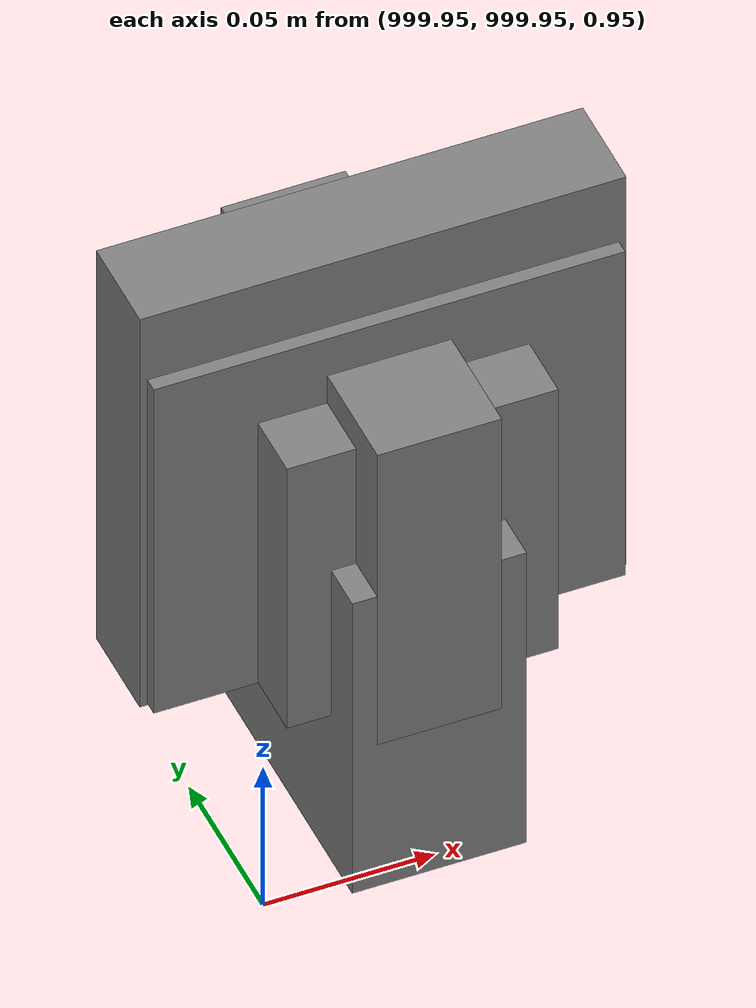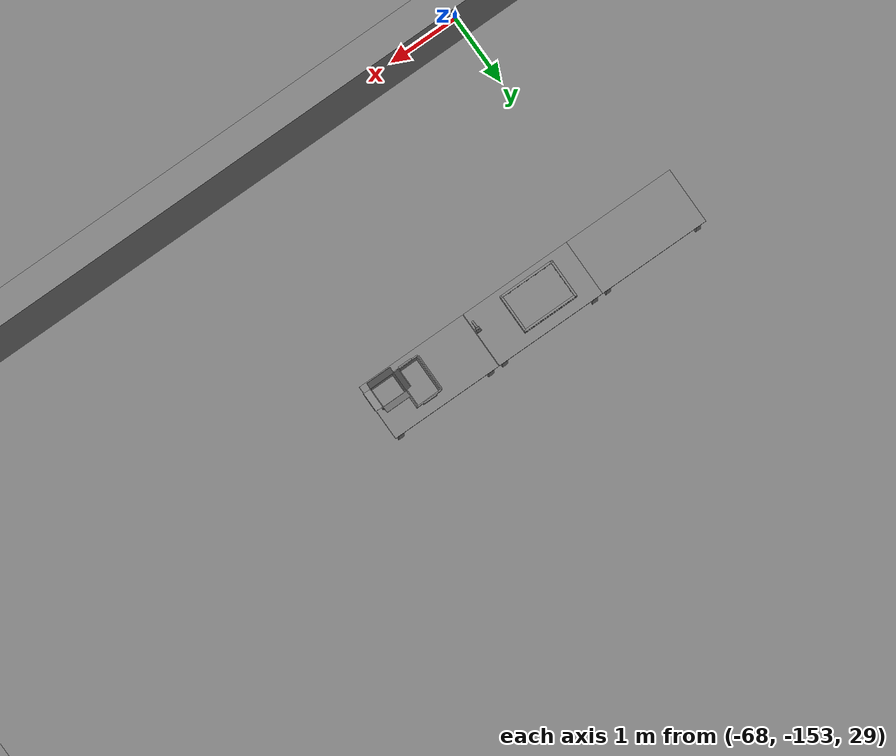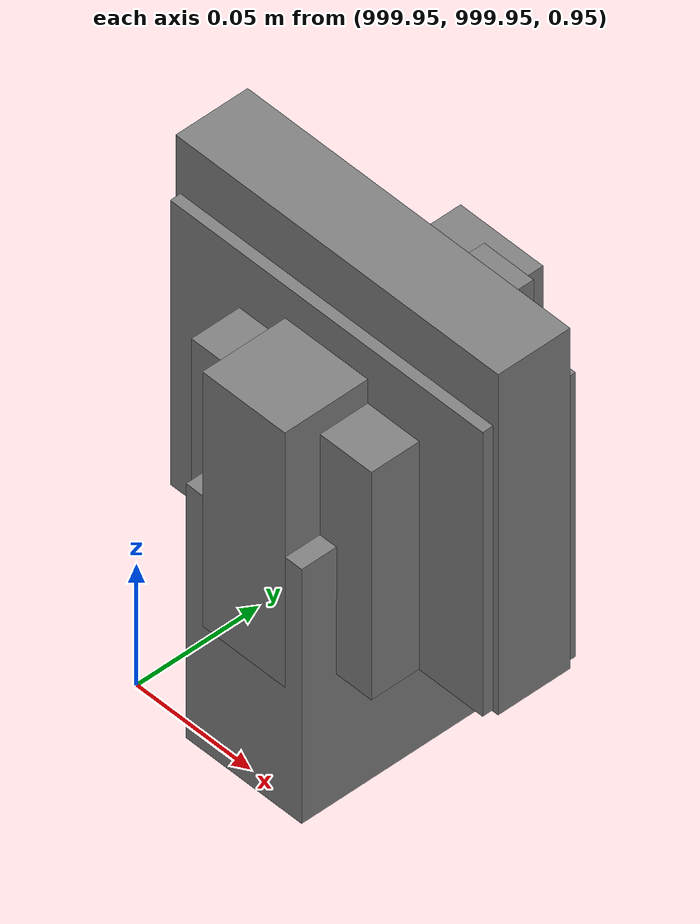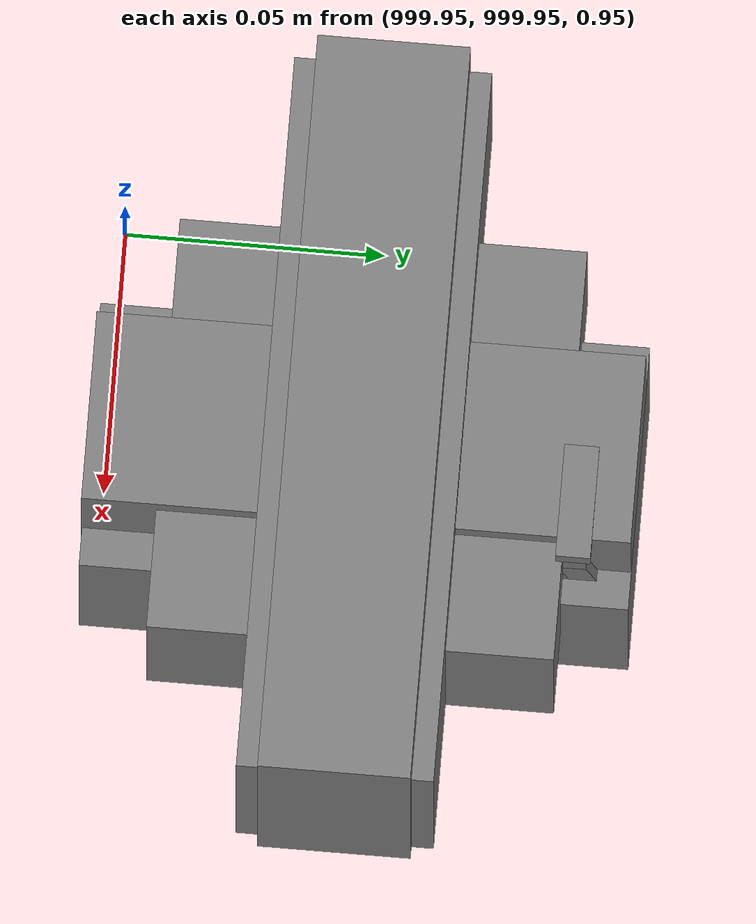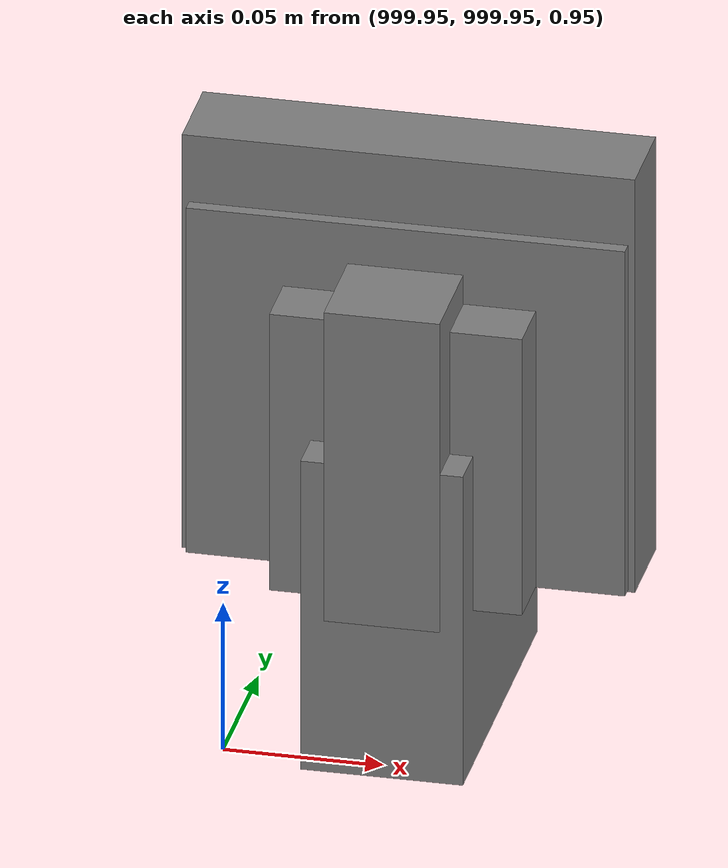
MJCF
<mujoco>
    <option gravity="0.000000000 0.000000000 -9.810000420" timestep="0.0049999999" integrator="implicitfast" density="1.225" viscosity="1.8000001e-05" noslip_iterations="10" iterations="100" sdf_iterations="50">
        <flag multiccd="disable"/>
    </option>
    <size memory="1000M"/>
    <compiler coordinate="local"/>
    <worldbody>
        <light cutoff="30" pos="0 1 1" dir="0 -1 -2"/>
        <light cutoff="30" pos="0 -1 1" dir="0 1 -2"/>
        <body pos="1000.000000000 1000.000000000 1.000000000" euler="0.000000000 0.000000000 180.000000000" name="openloong_gripper_2f85_fix_base_usda_wifi_box">
            <geom contype="1" conaffinity="1" density="1000" type="box" material="" rgba="0.500000000 0.500000000 0.500000000 1.000000000" solimp="0.899999976 0.949999988 0.001000000" friction="1.000000000 0.005000000 0.000100000" solref="0.020000000 1.000000000" margin="0" condim="3" group="0" pos="0.000000000 0.000000000 0.058978677" quat="0.000000000 0.000000047 0.000000000 1.000000000" size="0.068499997 0.018999999 0.059000000" name="openloong_gripper_2f85_fix_base_usda_geom_27CF793C_5222_4F17_B680_AC3684F4F340"/>
            <freejoint name="openloong_gripper_2f85_fix_base_usda_wifi_box_joint"/>
            <site size="0.005000000 0.005000000 0.005000000" rgba="0.500000000 0.500000000 0.500000000 1.000000000" pos="0.000000000 0.000000000 0.000000000" quat="0.999961913 0.008726500 0.000000000 0.000000000" group="0" type="sphere" name="openloong_gripper_2f85_fix_base_usda_wifi_boxsite"/>
        </body>
        <body pos="-66.023635864 -149.065307617 31.168725967" euler="-84.767158508 -22.271562576 30.626335144" mocap="true" name="spotlight1_SpotLight"/>
        <body pos="1000.000000000 1000.000000000 1.000000000" euler="0.000011953 0.000005123 -179.999984741" name="openloong_gripper_2f85_fix_base_usda_intel_box">
            <geom contype="1" conaffinity="1" density="1000" type="box" material="" rgba="0.500000000 0.500000000 0.500000000 1.000000000" solimp="0.899999976 0.949999988 0.001000000" friction="1.000000000 0.005000000 0.000100000" solref="0.020000000 1.000000000" margin="0" condim="3" group="0" pos="0.000000000 -0.000067139 0.000082284" quat="0.707106709 0.000000225 0.000000253 0.707106650" size="0.052800003 0.025300000 0.052800003" name="openloong_gripper_2f85_fix_base_usda_geom_B5DCE890_BB93_4C7E_A669_C83E202BA483"/>
            <freejoint name="openloong_gripper_2f85_fix_base_usda_intel_box_joint"/>
            <site size="0.005000000 0.005000000 0.005000000" rgba="0.500000000 0.500000000 0.500000000 1.000000000" pos="0.000000000 0.000000000 0.000000000" quat="0.999961913 0.008726500 0.000000000 0.000000000" group="0" type="sphere" name="openloong_gripper_2f85_fix_base_usda_intel_boxsite"/>
        </body>
        <body pos="-66.195693970 -149.069290161 31.170520782" euler="-174.014495850 87.545639038 -48.634716034" mocap="true" name="spotlight2_SpotLight"/>
        <body pos="-66.059402466 -149.325393677 31.162050247" euler="-18.588346481 72.597297668 22.762596130" mocap="true" name="spotlight3_SpotLight"/>
        <body pos="1000.000000000 999.999938965 1.000000000" euler="0.000000000 0.000000000 180.000000000" name="openloong_gripper_2f85_fix_base_usda_intelcore_i5">
            <geom contype="1" conaffinity="1" density="1000" type="box" material="" rgba="0.500000000 0.500000000 0.500000000 1.000000000" solimp="0.899999976 0.949999988 0.001000000" friction="1.000000000 0.005000000 0.000100000" solref="0.020000000 1.000000000" margin="0" condim="3" group="0" pos="0.000000000 0.000000000 0.051722717" quat="0.707106709 0.000000000 0.000000000 -0.707106769" size="0.052800000 0.018080002 0.052800000" name="openloong_gripper_2f85_fix_base_usda_geom_B5183401_4054_467B_8775_B5804C43D33D"/>
            <freejoint name="openloong_gripper_2f85_fix_base_usda_intelcore_i5_joint"/>
            <site size="0.005000000 0.005000000 0.005000000" rgba="0.500000000 0.500000000 0.500000000 1.000000000" pos="0.000000000 0.000000000 0.000000000" quat="0.999961913 0.008726534 0.000000000 0.000000000" group="0" type="sphere" name="openloong_gripper_2f85_fix_base_usda_intelcore_i5site"/>
        </body>
        <body pos="1000.000000000 1000.000000000 1.000000000" euler="0.000000000 0.000000000 180.000000000" name="openloong_gripper_2f85_fix_base_usda_cpu_fan">
            <geom contype="1" conaffinity="1" density="1000" type="box" material="" rgba="0.500000000 0.500000000 0.500000000 1.000000000" solimp="0.899999976 0.949999988 0.001000000" friction="1.000000000 0.005000000 0.000100000" solref="0.020000000 1.000000000" margin="0" condim="3" group="0" pos="0.000000000 0.000000000 0.070034981" quat="0.000000000 0.000000000 0.000000000 1.000000000" size="0.070700005 0.014699999 0.070700005" name="openloong_gripper_2f85_fix_base_usda_geom_F3136673_9D3B_4F23_867E_E5F37F0D7C53"/>
            <freejoint name="openloong_gripper_2f85_fix_base_usda_cpu_fan_joint"/>
            <site size="0.005000000 0.005000000 0.005000000" rgba="0.500000000 0.500000000 0.500000000 1.000000000" pos="0.000000000 0.000000000 0.000000000" quat="0.999961913 0.008726535 0.000000000 0.000000000" group="0" type="sphere" name="openloong_gripper_2f85_fix_base_usda_cpu_fancsite"/>
        </body>
        <body pos="1000.000000000 1000.000000000 1.000000000" euler="0.000000000 0.000000000 180.000000000" name="openloong_gripper_2f85_fix_base_usda_battery_01">
            <geom contype="1" conaffinity="1" density="1000" type="box" material="" rgba="0.500000000 0.500000000 0.500000000 1.000000000" solimp="0.899999976 0.949999988 0.001000000" friction="1.000000000 0.005000000 0.000100000" solref="0.020000000 1.000000000" margin="0" condim="3" group="0" pos="-0.011123657 -0.041940309 0.101691343" quat="1.000000000 0.000000000 0.000000000 0.000000000" size="0.010800000 0.003375000 0.004725000" name="openloong_gripper_2f85_fix_base_usda_geom_72E4B74C_22F5_4B0F_AC0F_3BD562653369"/>
            <geom contype="1" conaffinity="1" density="1000" type="box" material="" rgba="0.500000000 0.500000000 0.500000000 1.000000000" solimp="0.899999976 0.949999988 0.001000000" friction="1.000000000 0.005000000 0.000100000" solref="0.020000000 1.000000000" margin="0" condim="3" group="0" pos="-0.010876465 -0.044247437 0.047066893" quat="0.998702705 -0.050920475 0.000000000 0.000000000" size="0.009450001 0.002700000 0.024975000" name="openloong_gripper_2f85_fix_base_usda_geom_644C979D_7135_44ED_9893_98764CE6217E"/>
            <geom contype="1" conaffinity="1" density="1000" type="box" material="" rgba="0.500000000 0.500000000 0.500000000 1.000000000" solimp="0.899999976 0.949999988 0.001000000" friction="1.000000000 0.005000000 0.000100000" solref="0.020000000 1.000000000" margin="0" condim="3" group="0" pos="-0.001235962 -0.000659180 0.047381196" quat="1.000000000 0.000000000 0.000000000 0.000000000" size="0.039420001 0.039150000 0.047250003" name="openloong_gripper_2f85_fix_base_usda_geom_26AA1BD5_8C18_4A46_BBBE_849AB3DA788B"/>
            <geom contype="1" conaffinity="1" density="1000" type="box" material="" rgba="0.500000000 0.500000000 0.500000000 1.000000000" solimp="0.899999976 0.949999988 0.001000000" friction="1.000000000 0.005000000 0.000100000" solref="0.020000000 1.000000000" margin="0" condim="3" group="0" pos="-0.010876465 -0.039138794 0.009851727" quat="1.000000000 0.000000000 0.000000000 0.000000000" size="0.009450001 0.010800000 0.013500000" name="openloong_gripper_2f85_fix_base_usda_geom_AA0E7E64_8BFB_487B_BC7D_5FA23B9DBC38"/>
            <geom contype="1" conaffinity="1" density="1000" type="box" material="" rgba="0.500000000 0.500000000 0.500000000 1.000000000" solimp="0.899999976 0.949999988 0.001000000" friction="1.000000000 0.005000000 0.000100000" solref="0.020000000 1.000000000" margin="0" condim="3" group="0" pos="-0.010876465 -0.041528322 0.071508206" quat="1.000000000 0.000000000 0.000000000 0.000000000" size="0.009450001 0.002700000 0.027000001" name="openloong_gripper_2f85_fix_base_usda_geom_A86B3423_D893_4CB1_BF18_5A163B12BC22"/>
            <freejoint name="openloong_gripper_2f85_fix_base_usda_battery_01_joint"/>
            <site size="0.005000000 0.005000000 0.005000000" rgba="0.500000000 0.500000000 0.500000000 1.000000000" pos="0.000000000 0.000000000 0.000000000" quat="0.999961913 0.008726500 0.000000000 0.000000000" group="0" type="sphere" name="openloong_gripper_2f85_fix_base_usda_battery_01site"/>
        </body>
        <body pos="-64.866622925 -149.383972168 30.183746338" euler="89.999984741 89.999946594 0.000000000" name="openloong_gripper_2f85_fix_base_usda_bluebox_01">
            <geom contype="1" conaffinity="1" density="1000" type="box" material="" rgba="0.500000000 0.500000000 0.500000000 1.000000000" solimp="0.899999976 0.949999988 0.001000000" friction="1.000000000 0.005000000 0.000100000" solref="0.020000000 1.000000000" margin="0" condim="3" group="0" pos="0.276580811 0.187225342 0.000068665" quat="0.707106948 0.000077471 0.707106352 0.000077486" size="0.100000001 0.057999998 0.010000000" name="openloong_gripper_2f85_fix_base_usda_geom_8739C846_B55D_48B6_9B05_FFC8B3C8AD9E"/>
            <geom contype="1" conaffinity="1" density="1000" type="box" material="" rgba="0.500000000 0.500000000 0.500000000 1.000000000" solimp="0.899999976 0.949999988 0.001000000" friction="1.000000000 0.005000000 0.000100000" solref="0.020000000 1.000000000" margin="0" condim="3" group="0" pos="0.000000000 0.002883911 0.000000000" quat="0.999999881 0.000000000 0.000000000 0.000000000" size="0.254000008 0.003000000 0.172000006" name="openloong_gripper_2f85_fix_base_usda_geom_BA855BA0_D1E8_447E_8908_FF6377CA9114"/>
            <geom contype="1" conaffinity="1" density="1000" type="box" material="" rgba="0.500000000 0.500000000 0.500000000 1.000000000" solimp="0.899999976 0.949999988 0.001000000" friction="1.000000000 0.005000000 0.000100000" solref="0.020000000 1.000000000" margin="0" condim="3" group="0" pos="0.000000000 0.124874115 0.173484802" quat="0.999796331 0.020176515 -0.000000015 0.000000030" size="0.259999990 0.119999997 0.007000000" name="openloong_gripper_2f85_fix_base_usda_geom_C8CAD4FE_71FC_4D70_B7CF_BA2044024FC7"/>
            <geom contype="1" conaffinity="1" density="1000" type="box" material="" rgba="0.500000000 0.500000000 0.500000000 1.000000000" solimp="0.899999976 0.949999988 0.001000000" friction="1.000000000 0.005000000 0.000100000" solref="0.020000000 1.000000000" margin="0" condim="3" group="0" pos="0.000000000 0.124874115 -0.173469543" quat="0.999796331 -0.020176545 -0.000000015 0.000000000" size="0.259999990 0.119999997 0.007000000" name="openloong_gripper_2f85_fix_base_usda_geom_A0736F79_4C97_4FEF_A6C6_B592D46B8480"/>
            <geom contype="1" conaffinity="1" density="1000" type="box" material="" rgba="0.500000000 0.500000000 0.500000000 1.000000000" solimp="0.899999976 0.949999988 0.001000000" friction="1.000000000 0.005000000 0.000100000" solref="0.020000000 1.000000000" margin="0" condim="3" group="0" pos="0.000000000 0.214008331 0.188980103" quat="0.999912977 0.013176724 0.000000015 0.000000000" size="0.259999990 0.029999999 0.012500000" name="openloong_gripper_2f85_fix_base_usda_geom_EFF97B0F_A1C1_4C5D_8D5D_FD49E74A0A0B"/>
            <geom contype="1" conaffinity="1" density="1000" type="box" material="" rgba="0.500000000 0.500000000 0.500000000 1.000000000" solimp="0.899999976 0.949999988 0.001000000" friction="1.000000000 0.005000000 0.000100000" solref="0.020000000 1.000000000" margin="0" condim="3" group="0" pos="-0.258361816 0.125289917 0.001876831" quat="0.702796936 -0.020792112 0.710783124 0.020769298" size="0.189999998 0.119999997 0.009000000" name="openloong_gripper_2f85_fix_base_usda_geom_03B7F3D4_64C5_4B3C_A6E4_056CE15F0780"/>
            <geom contype="1" conaffinity="1" density="1000" type="box" material="" rgba="0.500000000 0.500000000 0.500000000 1.000000000" solimp="0.899999976 0.949999988 0.001000000" friction="1.000000000 0.005000000 0.000100000" solref="0.020000000 1.000000000" margin="0" condim="3" group="0" pos="0.000000000 0.214008331 -0.188980103" quat="0.999912977 -0.013176769 0.000000030 0.000000015" size="0.259999990 0.029999999 0.012500000" name="openloong_gripper_2f85_fix_base_usda_geom_CAD667E3_288D_4B2C_952D_4DF814ABB650"/>
            <geom contype="1" conaffinity="1" density="1000" type="box" material="" rgba="0.500000000 0.500000000 0.500000000 1.000000000" solimp="0.899999976 0.949999988 0.001000000" friction="1.000000000 0.005000000 0.000100000" solref="0.020000000 1.000000000" margin="0" condim="3" group="0" pos="-0.276611328 0.187225342 0.000068665" quat="0.707106650 0.000077441 0.707106709 0.000077456" size="0.100000001 0.057999998 0.010000000" name="openloong_gripper_2f85_fix_base_usda_geom_F154FAA8_7DB0_4080_8424_5758855175D2"/>
            <geom contype="1" conaffinity="1" density="1000" type="box" material="" rgba="0.500000000 0.500000000 0.500000000 1.000000000" solimp="0.899999976 0.949999988 0.001000000" friction="1.000000000 0.005000000 0.000100000" solref="0.020000000 1.000000000" margin="0" condim="3" group="0" pos="0.258331299 0.125289917 0.001876831" quat="0.702851415 0.018856421 0.710823774 -0.019329369" size="0.189999998 0.119999997 0.009000000" name="openloong_gripper_2f85_fix_base_usda_geom_0275CAB5_05AF_4749_AD08_80B7A74E94F5"/>
            <freejoint name="openloong_gripper_2f85_fix_base_usda_bluebox_01_joint"/>
            <site size="0.005000000 0.005000000 0.005000000" rgba="0.500000000 0.500000000 0.500000000 1.000000000" pos="0.000000000 0.000000000 0.000000000" quat="0.999961913 0.008726534 0.000000000 0.000000000" group="0" type="sphere" name="openloong_gripper_2f85_fix_base_usda_bluebox_01site"/>
        </body>
        <body pos="-64.496299744 -149.491867065 30.235729218" euler="0.000000000 0.000000000 89.999946594" name="openloong_gripper_2f85_fix_base_usda_cardboardbox_01">
            <geom contype="1" conaffinity="1" density="1000" type="box" material="" rgba="0.500000000 0.500000000 0.500000000 1.000000000" solimp="0.899999976 0.949999988 0.001000000" friction="1.000000000 0.005000000 0.000100000" solref="0.020000000 1.000000000" margin="0" condim="3" group="0" pos="-0.003166199 -0.004086494 0.005052090" quat="1.000000000 0.000000000 0.000000000 0.000000000" size="0.142499998 0.177500010 0.005000000" name="openloong_gripper_2f85_fix_base_usda_geom_F4E0C7EB_75F4_4DEE_BF05_DC64C03F33C2"/>
            <geom contype="1" conaffinity="1" density="1000" type="box" material="" rgba="0.500000000 0.500000000 0.500000000 1.000000000" solimp="0.899999976 0.949999988 0.001000000" friction="1.000000000 0.005000000 0.000100000" solref="0.020000000 1.000000000" margin="0" condim="3" group="0" pos="-0.003166199 0.170316696 0.150570869" quat="1.000000000 0.000000000 0.000000000 0.000000000" size="0.142499998 0.005000000 0.149999991" name="openloong_gripper_2f85_fix_base_usda_geom_26F8AF71_4556_4AC4_8238_BFDFEBC8CD0D"/>
            <geom contype="1" conaffinity="1" density="1000" type="box" material="" rgba="0.500000000 0.500000000 0.500000000 1.000000000" solimp="0.899999976 0.949999988 0.001000000" friction="1.000000000 0.005000000 0.000100000" solref="0.020000000 1.000000000" margin="0" condim="3" group="0" pos="-0.147399902 -0.005307198 0.150570869" quat="1.000000000 0.000000000 0.000000000 0.000000000" size="0.005000000 0.177500010 0.149999991" name="openloong_gripper_2f85_fix_base_usda_geom_06A326D2_4698_427C_A0EE_709697651A9E"/>
            <geom contype="1" conaffinity="1" density="1000" type="box" material="" rgba="0.500000000 0.500000000 0.500000000 1.000000000" solimp="0.899999976 0.949999988 0.001000000" friction="1.000000000 0.005000000 0.000100000" solref="0.020000000 1.000000000" margin="0" condim="3" group="0" pos="0.140275955 -0.005307198 0.150570869" quat="1.000000000 0.000000000 0.000000000 0.000000000" size="0.005000000 0.177500010 0.149999991" name="openloong_gripper_2f85_fix_base_usda_geom_28B7A689_16E2_4269_969D_18DF1403CA9D"/>
            <geom contype="1" conaffinity="1" density="1000" type="box" material="" rgba="0.500000000 0.500000000 0.500000000 1.000000000" solimp="0.899999976 0.949999988 0.001000000" friction="1.000000000 0.005000000 0.000100000" solref="0.020000000 1.000000000" margin="0" condim="3" group="0" pos="-0.003166199 -0.181550980 0.150570869" quat="1.000000000 0.000000000 0.000000000 0.000000000" size="0.142499998 0.005000000 0.149999991" name="openloong_gripper_2f85_fix_base_usda_geom_B621F45E_5F86_4537_A34C_D5C33CE83B4A"/>
            <freejoint name="openloong_gripper_2f85_fix_base_usda_cardboardbox_01_joint"/>
            <site size="0.005000000 0.005000000 0.005000000" rgba="0.500000000 0.500000000 0.500000000 1.000000000" pos="0.000000000 0.000000000 0.000000000" quat="0.999961913 0.008726535 0.000000000 0.000000000" group="0" type="sphere" name="openloong_gripper_2f85_fix_base_usda_site_3DC13356_19F4_47C8_B0EB_413F6709B853"/>
            <body pos="0.139160156 -0.004048347 0.301930904" euler="-179.999954224 49.383502960 179.999954224" name="openloong_gripper_2f85_fix_base_usda_A1_006">
                <geom contype="1" conaffinity="1" density="1000" type="box" material="" rgba="0.500000000 0.500000000 0.500000000 1.000000000" solimp="0.899999976 0.949999988 0.001000000" friction="1.000000000 0.005000000 0.000100000" solref="0.020000000 1.000000000" margin="0" condim="3" group="0" pos="-0.071587563 0.000009537 0.001745224" quat="0.999999881 0.000000000 0.000000000 0.000000000" size="0.071249999 0.179999992 0.002500000" name="openloong_gripper_2f85_fix_base_usda_geom_CF2A2FB2_5D4B_43D4_9ED4_1241283E113D"/>
                <joint armature="0" stiffness="0.07" damping="0.0099999998" axis="0.000000 1.000000 0.000000" type="hinge" name="openloong_gripper_2f85_fix_base_usda_A1_006"/>
            </body>
            <body pos="-0.145902634 -0.004086494 0.301938057" euler="-180.000000000 -60.000011444 -180.000000000" name="openloong_gripper_2f85_fix_base_usda_A2_006">
                <geom contype="1" conaffinity="1" density="1000" type="box" material="" rgba="0.500000000 0.500000000 0.500000000 1.000000000" solimp="0.899999976 0.949999988 0.001000000" friction="1.000000000 0.005000000 0.000100000" solref="0.020000000 1.000000000" margin="0" condim="3" group="0" pos="0.071268082 0.000009537 0.002717972" quat="0.000002921 0.000000000 -0.000000030 0.999999881" size="0.071249999 0.179999992 0.002500000" name="openloong_gripper_2f85_fix_base_usda_geom_324DB204_6474_4580_85B2_E3DD05AEA8DC"/>
                <joint armature="0" stiffness="0.07" damping="0.0099999998" axis="0.000000 1.000000 0.000000" type="hinge" name="openloong_gripper_2f85_fix_base_usda_A2_006"/>
            </body>
            <body pos="-0.003385544 0.175991058 0.301930904" euler="-125.858116150 -0.000004561 0.000002331" name="openloong_gripper_2f85_fix_base_usda_B2_006">
                <geom contype="1" conaffinity="1" density="1000" type="box" material="" rgba="0.500000000 0.500000000 0.500000000 1.000000000" solimp="0.899999976 0.949999988 0.001000000" friction="1.000000000 0.005000000 0.000100000" solref="0.020000000 1.000000000" margin="0" condim="3" group="0" pos="0.000009537 -0.070939064 -0.002470016" quat="0.999614120 0.027776197 -0.000000015 0.000000030" size="0.137500003 0.064999998 0.005000000" name="openloong_gripper_2f85_fix_base_usda_geom_CEFB9FE2_B659_46A6_AA1D_80DFAFDC35BA"/>
                <joint armature="0" stiffness="0.07" damping="0.0099999998" axis="1.000000 0.000000 0.000000" type="hinge" name="openloong_gripper_2f85_fix_base_usda_B2_006"/>
            </body>
            <body pos="-0.003385544 -0.184140205 0.301938057" euler="147.805557251 0.000000000 0.000000000" name="openloong_gripper_2f85_fix_base_usda_B1_006">
                <geom contype="1" conaffinity="1" density="1000" type="box" material="" rgba="0.500000000 0.500000000 0.500000000 1.000000000" solimp="0.899999976 0.949999988 0.001000000" friction="1.000000000 0.005000000 0.000100000" solref="0.020000000 1.000000000" margin="0" condim="3" group="0" pos="-0.000028610 0.070202351 -0.002703667" quat="0.999614179 -0.027776167 0.000000000 0.000000000" size="0.137500003 0.064999998 0.005000000" name="openloong_gripper_2f85_fix_base_usda_geom_19FE24AB_F373_4D37_B679_B12C9A30540D"/>
                <joint armature="0" stiffness="0.07" damping="0.0099999998" axis="1.000000 0.000000 0.000000" type="hinge" name="openloong_gripper_2f85_fix_base_usda_B1_006"/>
            </body>
        </body>
        <body pos="-65.882858276 -149.481979370 30.229999542" euler="-64.487716675 0.000000000 0.000000000" name="openloong_gripper_2f85_fix_base_usda_Barcode">
            <geom contype="1" conaffinity="1" density="1000" type="box" material="" rgba="0.500000000 0.500000000 0.500000000 1.000000000" solimp="0.899999976 0.949999988 0.001000000" friction="1.000000000 0.005000000 0.000100000" solref="0.020000000 1.000000000" margin="0" condim="3" group="0" pos="0.000000000 0.013038635 0.001419067" quat="0.000000000 0.000000000 0.000000000 1.000000119" size="0.034000002 0.010000000 0.017999999" name="openloong_gripper_2f85_fix_base_usda_geom_D61205E5_C210_489D_9228_650A56AFAEFE"/>
            <geom contype="1" conaffinity="1" density="1000" type="box" material="" rgba="0.500000000 0.500000000 0.500000000 1.000000000" solimp="0.899999976 0.949999988 0.001000000" friction="1.000000000 0.005000000 0.000100000" solref="0.020000000 1.000000000" margin="0" condim="3" group="0" pos="0.000000000 -0.035301208 -0.007095337" quat="0.000000000 0.000000000 -0.043619365 0.999048233" size="0.028999999 0.010000000 0.020000000" name="openloong_gripper_2f85_fix_base_usda_geom_5107DB8D_6824_4947_B615_7DE2AF56D919"/>
            <geom contype="1" conaffinity="1" density="1000" type="box" material="" rgba="0.500000000 0.500000000 0.500000000 1.000000000" solimp="0.899999976 0.949999988 0.001000000" friction="1.000000000 0.005000000 0.000100000" solref="0.020000000 1.000000000" margin="0" condim="3" group="0" pos="0.000000000 -0.043411255 -0.011749268" quat="0.922262907 0.386563420 0.000000000 0.000000000" size="0.026000001 0.010000000 0.020000000" name="openloong_gripper_2f85_fix_base_usda_geom_6D588B58_DB13_41C2_B9E1_081A8E3A0BF5"/>
            <geom contype="1" conaffinity="1" density="1000" type="box" material="" rgba="0.500000000 0.500000000 0.500000000 1.000000000" solimp="0.899999976 0.949999988 0.001000000" friction="1.000000000 0.005000000 0.000100000" solref="0.020000000 1.000000000" margin="0" condim="3" group="0" pos="0.000000000 -0.016967773 -0.031860352" quat="0.000000000 0.000000000 0.000000000 1.000000119" size="0.008000000 0.010000000 0.013000000" name="openloong_gripper_2f85_fix_base_usda_geom_788DC9B0_A18C_4B96_B9A5_5C1F82DB2173"/>
            <geom contype="1" conaffinity="1" density="1000" type="box" material="" rgba="0.500000000 0.500000000 0.500000000 1.000000000" solimp="0.899999976 0.949999988 0.001000000" friction="1.000000000 0.005000000 0.000100000" solref="0.020000000 1.000000000" margin="0" condim="3" group="0" pos="0.000000000 -0.001869202 0.000312805" quat="0.953716993 0.300705761 0.000000000 0.000000000" size="0.032000002 0.010000000 0.018999999" name="openloong_gripper_2f85_fix_base_usda_geom_7E89F84E_ACED_4A3B_B1C0_1E2E31C9818A"/>
            <geom contype="1" conaffinity="1" density="1000" type="box" material="" rgba="0.500000000 0.500000000 0.500000000 1.000000000" solimp="0.899999976 0.949999988 0.001000000" friction="1.000000000 0.005000000 0.000100000" solref="0.020000000 1.000000000" margin="0" condim="3" group="0" pos="0.000000000 -0.019531250 -0.003173828" quat="0.953716993 0.300705761 0.000000000 0.000000000" size="0.030999999 0.010000000 0.020000000" name="openloong_gripper_2f85_fix_base_usda_geom_C60FC6FE_DBCA_4E33_8CB6_32699FCC6480"/>
            <geom contype="1" conaffinity="1" density="1000" type="box" material="" rgba="0.500000000 0.500000000 0.500000000 1.000000000" solimp="0.899999976 0.949999988 0.001000000" friction="1.000000000 0.005000000 0.000100000" solref="0.020000000 1.000000000" margin="0" condim="3" group="0" pos="0.000000000 -0.035301208 -0.007095337" quat="0.953716993 0.300705761 0.000000000 0.000000000" size="0.028999999 0.010000000 0.020000000" name="openloong_gripper_2f85_fix_base_usda_geom_EA88DB0A_714E_48AF_B568_4A260A138646"/>
            <geom contype="1" conaffinity="1" density="1000" type="box" material="" rgba="0.500000000 0.500000000 0.500000000 1.000000000" solimp="0.899999976 0.949999988 0.001000000" friction="1.000000000 0.005000000 0.000100000" solref="0.020000000 1.000000000" margin="0" condim="3" group="0" pos="0.000000000 -0.042617798 -0.071121216" quat="0.000000000 0.000000000 0.000000000 1.000000119" size="0.013000000 0.021000000 0.059999999" name="openloong_gripper_2f85_fix_base_usda_geom_08E4AFFE_F8AD_4564_8382_82364FFAAFC4"/>
            <freejoint name="openloong_gripper_2f85_fix_base_usda_Barcode_joint"/>
            <site size="0.005000000 0.005000000 0.005000000" rgba="0.500000000 0.500000000 0.500000000 1.000000000" pos="0.000000000 0.000000000 0.000000000" quat="1.000000000 0.000000000 0.000000000 0.000000000" group="0" type="sphere" name="openloong_gripper_2f85_fix_base_usda_Barcode_site"/>
        </body>
        <body pos="-66.745018005 -149.392349243 30.184000015" euler="0.000000000 0.000000000 89.999946594" name="[22329843898165]_Basket_01">
            <geom contype="1" conaffinity="1" density="1000" type="box" material="" rgba="0.500000000 0.500000000 0.500000000 1.000000000" solimp="0.899999976 0.949999988 0.001000000" friction="1.000000000 0.005000000 0.000100000" solref="0.020000000 1.000000000" margin="0" condim="3" group="0" pos="-0.052425385 0.389207840 0.089787483" quat="0.707107008 0.000000000 0.000000000 0.707106411" size="0.014249999 0.014249999 0.059999999" name="[22329843898165]_geom_CD71F546_ACE4_4355_A036_B751736D3D25"/>
            <geom contype="1" conaffinity="1" density="1000" type="box" material="" rgba="0.500000000 0.500000000 0.500000000 1.000000000" solimp="0.899999976 0.949999988 0.001000000" friction="1.000000000 0.005000000 0.000100000" solref="0.020000000 1.000000000" margin="0" condim="3" group="0" pos="0.264015198 -0.133043289 0.089787483" quat="0.707107008 0.000000000 0.000000000 0.707106411" size="0.014249999 0.014249999 0.059999999" name="[22329843898165]_geom_76670580_8D51_4E23_A349_A4F7BC51F83D"/>
            <geom contype="1" conaffinity="1" density="1000" type="box" material="" rgba="0.500000000 0.500000000 0.500000000 1.000000000" solimp="0.899999976 0.949999988 0.001000000" friction="1.000000000 0.005000000 0.000100000" solref="0.020000000 1.000000000" margin="0" condim="3" group="0" pos="-0.264015198 -0.265548706 0.089793205" quat="0.707107008 0.000000000 0.000000000 0.707106411" size="0.014249999 0.014249999 0.059999999" name="[22329843898165]_geom_2BCD7EFD_90CF_4A94_9B8B_C0AB2F21C73D"/>
            <geom contype="1" conaffinity="1" density="1000" type="box" material="" rgba="0.500000000 0.500000000 0.500000000 1.000000000" solimp="0.899999976 0.949999988 0.001000000" friction="1.000000000 0.005000000 0.000100000" solref="0.020000000 1.000000000" margin="0" condim="3" group="0" pos="-0.160263062 -0.389322281 0.089793205" quat="0.707107008 0.000000000 0.000000000 0.707106411" size="0.014249999 0.014249999 0.059999999" name="[22329843898165]_geom_9BAFCFF3_4630_4163_B189_A70F77A2E972"/>
            <geom contype="1" conaffinity="1" density="1000" type="box" material="" rgba="0.500000000 0.500000000 0.500000000 1.000000000" solimp="0.899999976 0.949999988 0.001000000" friction="1.000000000 0.005000000 0.000100000" solref="0.020000000 1.000000000" margin="0" condim="3" group="0" pos="0.162265778 -0.389322281 0.089787483" quat="0.707107008 0.000000000 0.000000000 0.707106411" size="0.014249999 0.014249999 0.059999999" name="[22329843898165]_geom_A7775A45_34C5_45EA_A864_1F9A70209AC5"/>
            <geom contype="1" conaffinity="1" density="1000" type="box" material="" rgba="0.500000000 0.500000000 0.500000000 1.000000000" solimp="0.899999976 0.949999988 0.001000000" friction="1.000000000 0.005000000 0.000100000" solref="0.020000000 1.000000000" margin="0" condim="3" group="0" pos="0.264015198 0.389207840 0.089787483" quat="0.707107008 0.000000000 0.000000000 0.707106411" size="0.014249999 0.014249999 0.059999999" name="[22329843898165]_geom_39E9E3B5_E033_4C81_BB92_049122AE6608"/>
            <geom contype="1" conaffinity="1" density="1000" type="box" material="" rgba="0.500000000 0.500000000 0.500000000 1.000000000" solimp="0.899999976 0.949999988 0.001000000" friction="1.000000000 0.005000000 0.000100000" solref="0.020000000 1.000000000" margin="0" condim="3" group="0" pos="-0.264015198 -0.133043289 0.089793205" quat="0.707107008 0.000000000 0.000000000 0.707106411" size="0.014249999 0.014249999 0.059999999" name="[22329843898165]_geom_876FD65E_7B9C_4265_A44E_343041D0BD39"/>
            <geom contype="1" conaffinity="1" density="1000" type="box" material="" rgba="0.500000000 0.500000000 0.500000000 1.000000000" solimp="0.899999976 0.949999988 0.001000000" friction="1.000000000 0.005000000 0.000100000" solref="0.020000000 1.000000000" margin="0" condim="3" group="0" pos="-0.264026642 0.269256592 0.089793205" quat="0.707107008 0.000000000 0.000000000 0.707106411" size="0.014249999 0.014249999 0.059999999" name="[22329843898165]_geom_89A98CAA_6880_4CEA_A0A3_14AC0957C0BE"/>
            <geom contype="1" conaffinity="1" density="1000" type="box" material="" rgba="0.500000000 0.500000000 0.500000000 1.000000000" solimp="0.899999976 0.949999988 0.001000000" friction="1.000000000 0.005000000 0.000100000" solref="0.020000000 1.000000000" margin="0" condim="3" group="0" pos="0.054462433 0.389207840 0.089787483" quat="0.707107008 0.000000000 0.000000000 0.707106411" size="0.014249999 0.014249999 0.059999999" name="[22329843898165]_geom_3157ABCF_BB8F_48C4_B9AF_BE37D7091A96"/>
            <geom contype="1" conaffinity="1" density="1000" type="box" material="" rgba="0.500000000 0.500000000 0.500000000 1.000000000" solimp="0.899999976 0.949999988 0.001000000" friction="1.000000000 0.005000000 0.000100000" solref="0.020000000 1.000000000" margin="0" condim="3" group="0" pos="0.054462433 -0.389322281 0.089787483" quat="0.707107008 0.000000000 0.000000000 0.707106411" size="0.014249999 0.014249999 0.059999999" name="[22329843898165]_geom_99F54F74_050F_46CA_BE5F_94AA386B1DCE"/>
            <geom contype="1" conaffinity="1" density="1000" type="box" material="" rgba="0.500000000 0.500000000 0.500000000 1.000000000" solimp="0.899999976 0.949999988 0.001000000" friction="1.000000000 0.005000000 0.000100000" solref="0.020000000 1.000000000" margin="0" condim="3" group="0" pos="0.264015198 0.269256592 0.089793205" quat="0.707107008 0.000000000 0.000000000 0.707106411" size="0.014249999 0.014249999 0.059999999" name="[22329843898165]_geom_FA31BC9B_393B_4184_ABB9_8930F2439920"/>
            <geom contype="1" conaffinity="1" density="1000" type="box" material="" rgba="0.500000000 0.500000000 0.500000000 1.000000000" solimp="0.899999976 0.949999988 0.001000000" friction="1.000000000 0.005000000 0.000100000" solref="0.020000000 1.000000000" margin="0" condim="3" group="0" pos="0.264015198 -0.389322281 0.089787483" quat="0.707107008 0.000000000 0.000000000 0.707106411" size="0.014249999 0.014249999 0.059999999" name="[22329843898165]_geom_FBEB0F55_3DE7_422C_9A15_C967B7E4B82B"/>
            <geom contype="1" conaffinity="1" density="1000" type="box" material="" rgba="0.500000000 0.500000000 0.500000000 1.000000000" solimp="0.899999976 0.949999988 0.001000000" friction="1.000000000 0.005000000 0.000100000" solref="0.020000000 1.000000000" margin="0" condim="3" group="0" pos="0.000000000 0.000000000 0.015998840" quat="0.707107008 0.000000000 0.000000000 0.707106411" size="0.403499991 0.279000014 0.015750000" name="[22329843898165]_geom_15BA8080_889C_4811_BC23_4D173586B66D"/>
            <geom contype="1" conaffinity="1" density="1000" type="box" material="" rgba="0.500000000 0.500000000 0.500000000 1.000000000" solimp="0.899999976 0.949999988 0.001000000" friction="1.000000000 0.005000000 0.000100000" solref="0.020000000 1.000000000" margin="0" condim="3" group="0" pos="0.000000000 -0.389476776 0.163619041" quat="0.707107008 0.000000000 0.000000000 0.707106411" size="0.015000000 0.277500004 0.015750000" name="[22329843898165]_geom_A3F8BD2A_2373_48C2_9EB8_47CAB83D6478"/>
            <geom contype="1" conaffinity="1" density="1000" type="box" material="" rgba="0.500000000 0.500000000 0.500000000 1.000000000" solimp="0.899999976 0.949999988 0.001000000" friction="1.000000000 0.005000000 0.000100000" solref="0.020000000 1.000000000" margin="0" condim="3" group="0" pos="0.162265778 0.389207840 0.089787483" quat="0.707107008 0.000000000 0.000000000 0.707106411" size="0.014249999 0.014249999 0.059999999" name="[22329843898165]_geom_35DCD268_A37A_49E6_9D5A_DBCB37E84156"/>
            <geom contype="1" conaffinity="1" density="1000" type="box" material="" rgba="0.500000000 0.500000000 0.500000000 1.000000000" solimp="0.899999976 0.949999988 0.001000000" friction="1.000000000 0.005000000 0.000100000" solref="0.020000000 1.000000000" margin="0" condim="3" group="0" pos="0.000000000 0.389471054 0.163619041" quat="0.707107008 0.000000000 0.000000000 0.707106411" size="0.015000000 0.277500004 0.015750000" name="[22329843898165]_geom_8B3D2C7D_4BB5_4046_9F99_9FC900423F0E"/>
            <geom contype="1" conaffinity="1" density="1000" type="box" material="" rgba="0.500000000 0.500000000 0.500000000 1.000000000" solimp="0.899999976 0.949999988 0.001000000" friction="1.000000000 0.005000000 0.000100000" solref="0.020000000 1.000000000" margin="0" condim="3" group="0" pos="-0.263511658 0.000000000 0.163619041" quat="0.707107008 0.000000000 0.000000000 0.707106411" size="0.403499991 0.015000000 0.015750000" name="[22329843898165]_geom_8FA89623_DB22_4982_9DC6_B5F32DE31561"/>
            <geom contype="1" conaffinity="1" density="1000" type="box" material="" rgba="0.500000000 0.500000000 0.500000000 1.000000000" solimp="0.899999976 0.949999988 0.001000000" friction="1.000000000 0.005000000 0.000100000" solref="0.020000000 1.000000000" margin="0" condim="3" group="0" pos="-0.264015198 0.141334534 0.089793205" quat="0.707107008 0.000000000 0.000000000 0.707106411" size="0.014249999 0.014249999 0.059999999" name="[22329843898165]_geom_2B128A6D_E207_4CE8_8B28_A7ED5FFE567B"/>
            <geom contype="1" conaffinity="1" density="1000" type="box" material="" rgba="0.500000000 0.500000000 0.500000000 1.000000000" solimp="0.899999976 0.949999988 0.001000000" friction="1.000000000 0.005000000 0.000100000" solref="0.020000000 1.000000000" margin="0" condim="3" group="0" pos="0.264015198 -0.265548706 0.089787483" quat="0.707107008 0.000000000 0.000000000 0.707106411" size="0.014249999 0.014249999 0.059999999" name="[22329843898165]_geom_1E379974_8A68_43C2_833E_269E75829980"/>
            <geom contype="1" conaffinity="1" density="1000" type="box" material="" rgba="0.500000000 0.500000000 0.500000000 1.000000000" solimp="0.899999976 0.949999988 0.001000000" friction="1.000000000 0.005000000 0.000100000" solref="0.020000000 1.000000000" margin="0" condim="3" group="0" pos="-0.160263062 0.389207840 0.089787483" quat="0.707107008 0.000000000 0.000000000 0.707106411" size="0.014249999 0.014249999 0.059999999" name="[22329843898165]_geom_168C7730_0D0A_44D6_939B_B22BF8A43833"/>
            <geom contype="1" conaffinity="1" density="1000" type="box" material="" rgba="0.500000000 0.500000000 0.500000000 1.000000000" solimp="0.899999976 0.949999988 0.001000000" friction="1.000000000 0.005000000 0.000100000" solref="0.020000000 1.000000000" margin="0" condim="3" group="0" pos="-0.052425385 -0.389322281 0.089787483" quat="0.707107008 0.000000000 0.000000000 0.707106411" size="0.014249999 0.014249999 0.059999999" name="[22329843898165]_geom_C854BFE2_10D4_48B9_A7BC_302967665384"/>
            <geom contype="1" conaffinity="1" density="1000" type="box" material="" rgba="0.500000000 0.500000000 0.500000000 1.000000000" solimp="0.899999976 0.949999988 0.001000000" friction="1.000000000 0.005000000 0.000100000" solref="0.020000000 1.000000000" margin="0" condim="3" group="0" pos="-0.264026642 -0.389322281 0.089793205" quat="0.707107008 0.000000000 0.000000000 0.707106411" size="0.014249999 0.014249999 0.059999999" name="[22329843898165]_geom_A581734D_5485_4194_91A9_9EBB4CC6A269"/>
            <geom contype="1" conaffinity="1" density="1000" type="box" material="" rgba="0.500000000 0.500000000 0.500000000 1.000000000" solimp="0.899999976 0.949999988 0.001000000" friction="1.000000000 0.005000000 0.000100000" solref="0.020000000 1.000000000" margin="0" condim="3" group="0" pos="0.264015198 0.141334534 0.089787483" quat="0.707107008 0.000000000 0.000000000 0.707106411" size="0.014249999 0.014249999 0.059999999" name="[22329843898165]_geom_DD8C7895_3636_4549_A09D_A302FEBFE564"/>
            <geom contype="1" conaffinity="1" density="1000" type="box" material="" rgba="0.500000000 0.500000000 0.500000000 1.000000000" solimp="0.899999976 0.949999988 0.001000000" friction="1.000000000 0.005000000 0.000100000" solref="0.020000000 1.000000000" margin="0" condim="3" group="0" pos="-0.264015198 0.389207840 0.089793205" quat="0.707107008 0.000000000 0.000000000 0.707106411" size="0.014249999 0.014249999 0.059999999" name="[22329843898165]_geom_4614A548_A844_42FE_B563_A2BF83D28F81"/>
            <geom contype="1" conaffinity="1" density="1000" type="box" material="" rgba="0.500000000 0.500000000 0.500000000 1.000000000" solimp="0.899999976 0.949999988 0.001000000" friction="1.000000000 0.005000000 0.000100000" solref="0.020000000 1.000000000" margin="0" condim="3" group="0" pos="0.264015198 0.004480362 0.089787483" quat="0.707107008 0.000000000 0.000000000 0.707106411" size="0.014249999 0.014249999 0.059999999" name="[22329843898165]_geom_EA0A8274_9EAC_4738_8D60_9CA3A1A9B1D4"/>
            <geom contype="1" conaffinity="1" density="1000" type="box" material="" rgba="0.500000000 0.500000000 0.500000000 1.000000000" solimp="0.899999976 0.949999988 0.001000000" friction="1.000000000 0.005000000 0.000100000" solref="0.020000000 1.000000000" margin="0" condim="3" group="0" pos="0.263694763 -0.000011444 0.163619041" quat="0.707107008 0.000000000 0.000000000 0.707106411" size="0.403499991 0.015000000 0.015750000" name="[22329843898165]_geom_6374CEFF_B513_4661_A850_6EB0C17AC44F"/>
            <geom contype="1" conaffinity="1" density="1000" type="box" material="" rgba="0.500000000 0.500000000 0.500000000 1.000000000" solimp="0.899999976 0.949999988 0.001000000" friction="1.000000000 0.005000000 0.000100000" solref="0.020000000 1.000000000" margin="0" condim="3" group="0" pos="-0.264015198 0.004480362 0.089793205" quat="0.707107008 0.000000000 0.000000000 0.707106411" size="0.014249999 0.014249999 0.059999999" name="[22329843898165]_geom_E4F9973E_37A9_47FA_B3FF_E117D04BBD3A"/>
            <freejoint name="[22329843898165]_joint_EC18CDBA_C8EF_4962_A170_595CDDA096AC"/>
        </body>
        <body pos="0.000000000 0.000000000 0.000000000" euler="0.000000000 0.000000000 0.000000000" name="Static Objects_Static Objects">
            <geom contype="1" conaffinity="1" density="1000" type="box" material="" rgba="0.500000000 0.500000000 0.500000000 1.000000000" solimp="0.899999976 0.949999988 0.001000000" friction="1.000000000 0.005000000 0.000100000" solref="0.020000000 1.000000000" margin="0" condim="3" group="0" pos="-67.544113159 -149.365814209 29.727830887" quat="0.500000417 0.499999970 0.499999553 0.499999970" size="0.381000012 0.319999993 0.041000001" name="Static Objects_geom_F7CD4BA4_E1D4_4BD1_9675_B94E1BA95598"/>
            <geom contype="1" conaffinity="1" density="1000" type="box" material="" rgba="0.500000000 0.500000000 0.500000000 1.000000000" solimp="0.899999976 0.949999988 0.001000000" friction="1.000000000 0.005000000 0.000100000" solref="0.020000000 1.000000000" margin="0" condim="3" group="0" pos="-68.239501953 -149.365814209 30.086868286" quat="0.500000417 0.499999970 0.499999553 0.499999970" size="0.370999992 0.039500002 0.745000005" name="Static Objects_geom_85A6F889_FB63_4F52_B17F_3ABB02C55810"/>
            <geom contype="1" conaffinity="1" density="1000" type="box" material="" rgba="0.500000000 0.500000000 0.500000000 1.000000000" solimp="0.899999976 0.949999988 0.001000000" friction="1.000000000 0.005000000 0.000100000" solref="0.020000000 1.000000000" margin="0" condim="3" group="0" pos="-68.239501953 -149.365814209 30.147235870" quat="0.500000417 0.499999970 0.499999553 0.499999970" size="0.400000006 0.022000000 0.800000012" name="Static Objects_geom_96B27B66_66C0_42D8_B201_3A7B31ECFA77"/>
            <geom contype="1" conaffinity="1" density="1000" type="box" material="" rgba="0.500000000 0.500000000 0.500000000 1.000000000" solimp="0.899999976 0.949999988 0.001000000" friction="1.000000000 0.005000000 0.000100000" solref="0.020000000 1.000000000" margin="0" condim="3" group="0" pos="-68.934890747 -149.365814209 29.727830887" quat="0.500000417 0.499999970 0.499999553 0.499999970" size="0.381000012 0.319999993 0.041000001" name="Static Objects_geom_7D25DA42_2462_43B0_8E31_1D58D0722AAA"/>
            <geom contype="1" conaffinity="1" density="1000" type="box" material="" rgba="0.500000000 0.500000000 0.500000000 1.000000000" solimp="0.899999976 0.949999988 0.001000000" friction="1.000000000 0.005000000 0.000100000" solref="0.020000000 1.000000000" margin="0" condim="3" group="0" pos="-68.239501953 -149.365814209 29.561563492" quat="0.500000417 0.499999970 0.499999553 0.499999970" size="0.020000000 0.022000000 0.660000026" name="Static Objects_geom_FD6CBC7D_3B60_43AE_9A87_739DFD6D38AD"/>
            <geom contype="1" conaffinity="1" density="1000" type="box" material="" rgba="0.500000000 0.500000000 0.500000000 1.000000000" solimp="0.899999976 0.949999988 0.001000000" friction="1.000000000 0.005000000 0.000100000" solref="0.020000000 1.000000000" margin="0" condim="3" group="0" pos="-65.945671082 -149.365814209 29.727830887" quat="0.500000417 0.499999970 0.499999553 0.499999970" size="0.381000012 0.319999993 0.041000001" name="Static Objects_geom_12DC38AD_78A3_484C_B085_1AE1781A5595"/>
            <geom contype="1" conaffinity="1" density="1000" type="box" material="" rgba="0.500000000 0.500000000 0.500000000 1.000000000" solimp="0.899999976 0.949999988 0.001000000" friction="1.000000000 0.005000000 0.000100000" solref="0.020000000 1.000000000" margin="0" condim="3" group="0" pos="-66.641059875 -149.365814209 30.086868286" quat="0.500000417 0.499999970 0.499999553 0.499999970" size="0.370999992 0.039500002 0.745000005" name="Static Objects_geom_C1FA9172_0F2B_42FD_AE1B_024255CF4EE0"/>
            <geom contype="1" conaffinity="1" density="1000" type="box" material="" rgba="0.500000000 0.500000000 0.500000000 1.000000000" solimp="0.899999976 0.949999988 0.001000000" friction="1.000000000 0.005000000 0.000100000" solref="0.020000000 1.000000000" margin="0" condim="3" group="0" pos="-66.641059875 -149.365814209 30.147235870" quat="0.500000417 0.499999970 0.499999553 0.499999970" size="0.400000006 0.022000000 0.800000012" name="Static Objects_geom_62EE123C_57C1_4962_B9EC_82B7674766FC"/>
            <geom contype="1" conaffinity="1" density="1000" type="box" material="" rgba="0.500000000 0.500000000 0.500000000 1.000000000" solimp="0.899999976 0.949999988 0.001000000" friction="1.000000000 0.005000000 0.000100000" solref="0.020000000 1.000000000" margin="0" condim="3" group="0" pos="-67.336448669 -149.365814209 29.727830887" quat="0.500000417 0.499999970 0.499999553 0.499999970" size="0.381000012 0.319999993 0.041000001" name="Static Objects_geom_76847ABD_7B4C_47B4_A943_FDB6CC6B52D2"/>
            <geom contype="1" conaffinity="1" density="1000" type="box" material="" rgba="0.500000000 0.500000000 0.500000000 1.000000000" solimp="0.899999976 0.949999988 0.001000000" friction="1.000000000 0.005000000 0.000100000" solref="0.020000000 1.000000000" margin="0" condim="3" group="0" pos="-66.641059875 -149.365814209 29.561563492" quat="0.500000417 0.499999970 0.499999553 0.499999970" size="0.020000000 0.022000000 0.660000026" name="Static Objects_geom_6B6F0C59_CB44_4F49_BF67_A930C09DBED6"/>
            <geom contype="1" conaffinity="1" density="1000" type="box" material="" rgba="0.500000000 0.500000000 0.500000000 1.000000000" solimp="0.899999976 0.949999988 0.001000000" friction="1.000000000 0.005000000 0.000100000" solref="0.020000000 1.000000000" margin="0" condim="3" group="0" pos="-64.338577271 -149.365814209 29.727830887" quat="0.500000417 0.499999970 0.499999553 0.499999970" size="0.381000012 0.319999993 0.041000001" name="Static Objects_geom_FD6EB334_F384_419B_A6F5_13D07E3530BD"/>
            <geom contype="1" conaffinity="1" density="1000" type="box" material="" rgba="0.500000000 0.500000000 0.500000000 1.000000000" solimp="0.899999976 0.949999988 0.001000000" friction="1.000000000 0.005000000 0.000100000" solref="0.020000000 1.000000000" margin="0" condim="3" group="0" pos="-65.033966064 -149.365814209 30.086868286" quat="0.500000417 0.499999970 0.499999553 0.499999970" size="0.370999992 0.039500002 0.745000005" name="Static Objects_geom_E9FFA3F4_3D94_4539_B8E8_F25E99E3ABCE"/>
            <geom contype="1" conaffinity="1" density="1000" type="box" material="" rgba="0.500000000 0.500000000 0.500000000 1.000000000" solimp="0.899999976 0.949999988 0.001000000" friction="1.000000000 0.005000000 0.000100000" solref="0.020000000 1.000000000" margin="0" condim="3" group="0" pos="-65.033966064 -149.365814209 30.147235870" quat="0.500000417 0.499999970 0.499999553 0.499999970" size="0.400000006 0.022000000 0.800000012" name="Static Objects_geom_EBC49E74_82BC_4B01_95F5_9DD74A852F84"/>
            <geom contype="1" conaffinity="1" density="1000" type="box" material="" rgba="0.500000000 0.500000000 0.500000000 1.000000000" solimp="0.899999976 0.949999988 0.001000000" friction="1.000000000 0.005000000 0.000100000" solref="0.020000000 1.000000000" margin="0" condim="3" group="0" pos="-65.729354858 -149.365814209 29.727830887" quat="0.500000417 0.499999970 0.499999553 0.499999970" size="0.381000012 0.319999993 0.041000001" name="Static Objects_geom_53C9D06B_13D8_4DF4_BDBB_F999039159CF"/>
            <geom contype="1" conaffinity="1" density="1000" type="box" material="" rgba="0.500000000 0.500000000 0.500000000 1.000000000" solimp="0.899999976 0.949999988 0.001000000" friction="1.000000000 0.005000000 0.000100000" solref="0.020000000 1.000000000" margin="0" condim="3" group="0" pos="-65.033966064 -149.365814209 29.561563492" quat="0.500000417 0.499999970 0.499999553 0.499999970" size="0.020000000 0.022000000 0.660000026" name="Static Objects_geom_B3B43A8A_77E2_4569_9988_80419F60B3FC"/>
            <geom contype="1" conaffinity="1" density="1000" type="box" material="" rgba="0.500000000 0.500000000 0.500000000 1.000000000" solimp="0.899999976 0.949999988 0.001000000" friction="1.000000000 0.005000000 0.000100000" solref="0.020000000 1.000000000" margin="0" condim="3" group="0" pos="-61.754566193 -137.853729248 33.906845093" quat="0.707107067 0.000000000 0.000000000 0.707106471" size="0.759999990 0.759999990 4.500000000" name="Static Objects_geom_004FF3A8_D460_4B09_904E_94FF99370132"/>
            <geom contype="1" conaffinity="1" density="1000" type="box" material="" rgba="0.500000000 0.500000000 0.500000000 1.000000000" solimp="0.899999976 0.949999988 0.001000000" friction="1.000000000 0.005000000 0.000100000" solref="0.020000000 1.000000000" margin="0" condim="3" group="0" pos="-57.511135101 -144.927108765 31.707921982" quat="1.000000000 0.000000000 0.000000000 0.000000000" size="0.200000003 8.000000000 2.299999952" name="Static Objects_geom_5998A9F9_7A1E_4FD5_A7AE_E07FF0F2DA08"/>
            <geom contype="1" conaffinity="1" density="1000" type="box" material="" rgba="0.500000000 0.500000000 0.500000000 1.000000000" solimp="0.899999976 0.949999988 0.001000000" friction="1.000000000 0.005000000 0.000100000" solref="0.020000000 1.000000000" margin="0" condim="3" group="0" pos="-80.517646790 -157.574050903 31.688196182" quat="0.707107067 0.000000000 0.000000000 0.707106471" size="0.600000024 0.600000024 2.299999952" name="Static Objects_geom_BC324CFD_B538_47CA_83D0_DD73AF480C19"/>
            <geom contype="1" conaffinity="1" density="1000" type="box" material="" rgba="0.500000000 0.500000000 0.500000000 1.000000000" solimp="0.899999976 0.949999988 0.001000000" friction="1.000000000 0.005000000 0.000100000" solref="0.020000000 1.000000000" margin="0" condim="3" group="0" pos="-80.711044312 -147.414932251 31.666158676" quat="1.000000000 0.000000000 0.000000000 0.000000000" size="0.200000003 10.000000000 2.299999952" name="Static Objects_geom_86F2A825_1747_45F3_9C10_5F9376F0E9BC"/>
            <geom contype="1" conaffinity="1" density="1000" type="box" material="" rgba="0.500000000 0.500000000 0.500000000 1.000000000" solimp="0.899999976 0.949999988 0.001000000" friction="1.000000000 0.005000000 0.000100000" solref="0.020000000 1.000000000" margin="0" condim="3" group="0" pos="-57.687217712 -137.434692383 31.688196182" quat="0.707107067 0.000000000 0.000000000 0.707106471" size="0.600000024 0.600000024 2.299999952" name="Static Objects_geom_6D6F3334_F131_4A79_86E7_F6E9F20E308C"/>
            <geom contype="1" conaffinity="1" density="1000" type="box" material="" rgba="0.500000000 0.500000000 0.500000000 1.000000000" solimp="0.899999976 0.949999988 0.001000000" friction="1.000000000 0.005000000 0.000100000" solref="0.020000000 1.000000000" margin="0" condim="3" group="0" pos="-69.537033081 -140.263229370 31.714921951" quat="0.707107067 0.000000000 0.000000000 0.707106471" size="0.759999990 4.500000000 2.299999952" name="Static Objects_geom_D07714E0_4DBF_4538_9D7D_645827A13CAE"/>
            <geom contype="1" conaffinity="1" density="1000" type="box" material="" rgba="0.500000000 0.500000000 0.500000000 1.000000000" solimp="0.899999976 0.949999988 0.001000000" friction="1.000000000 0.005000000 0.000100000" solref="0.020000000 1.000000000" margin="0" condim="3" group="0" pos="-80.073638916 -137.853713989 33.906845093" quat="0.707107067 0.000000000 0.000000000 0.707106471" size="0.759999990 0.759999990 4.500000000" name="Static Objects_geom_2241CF33_6635_49AB_89C0_5DBA2BF9B2D0"/>
            <geom contype="1" conaffinity="1" density="1000" type="box" material="" rgba="0.500000000 0.500000000 0.500000000 1.000000000" solimp="0.899999976 0.949999988 0.001000000" friction="1.000000000 0.005000000 0.000100000" solref="0.020000000 1.000000000" margin="0" condim="3" group="0" pos="-73.406707764 -155.734664917 31.707921982" quat="1.000000000 0.000000000 0.000000000 0.000000000" size="0.200000003 3.000000000 2.299999952" name="Static Objects_geom_114E9117_133C_45FB_81A5_EA0742846F7D"/>
            <geom contype="1" conaffinity="1" density="1000" type="box" material="" rgba="0.500000000 0.500000000 0.500000000 1.000000000" solimp="0.899999976 0.949999988 0.001000000" friction="1.000000000 0.005000000 0.000100000" solref="0.020000000 1.000000000" margin="0" condim="3" group="0" pos="-68.497543335 -137.448257446 31.707921982" quat="0.707107067 0.000000000 0.000000000 0.707106471" size="0.200000003 14.000000000 2.299999952" name="Static Objects_geom_E223F3F9_617E_4795_94BC_20F7C0A8649D"/>
            <geom contype="1" conaffinity="1" density="1000" type="cylinder" material="" rgba="0.500000000 0.500000000 0.500000000 1.000000000" solimp="0.899999976 0.949999988 0.001000000" friction="1.000000000 0.005000000 0.000100000" solref="0.020000000 1.000000000" margin="0" condim="3" group="0" pos="-68.868522644 -142.134506226 31.711090088" quat="0.707107067 0.000000000 0.000000000 0.707106471" size="0.509999990 2.299999952 1.000000000" name="Static Objects_geom_DC0BAA4C_77DC_4C35_9E8D_778F4CBE7989"/>
            <geom contype="1" conaffinity="1" density="1000" type="plane" material="" rgba="0.500000000 0.500000000 0.500000000 1.000000000" solimp="0.899999976 0.949999988 0.001000000" friction="1.000000000 0.005000000 0.000100000" solref="0.020000000 1.000000000" margin="0" condim="3" group="0" pos="-72.873703003 -147.131927490 29.409669876" quat="1.000000000 0.000000000 0.000000000 0.000000000" size="18.000000000 14.000000000 1.000000000" name="Static Objects_geom_8A47539F_EE05_4A74_88CA_90905419FB34"/>
            <geom contype="1" conaffinity="1" density="1000" type="box" material="" rgba="0.500000000 0.500000000 0.500000000 1.000000000" solimp="0.899999976 0.949999988 0.001000000" friction="1.000000000 0.005000000 0.000100000" solref="0.020000000 1.000000000" margin="0" condim="3" group="0" pos="-79.943580627 -157.782272339 31.707921982" quat="0.707107067 0.000000000 0.000000000 0.707106471" size="0.200000003 7.000000000 2.299999952" name="Static Objects_geom_8AD2D852_E1C2_4288_AC75_112D1457C7E6"/>
            <geom contype="1" conaffinity="1" density="1000" type="box" material="" rgba="0.500000000 0.500000000 0.500000000 1.000000000" solimp="0.899999976 0.949999988 0.001000000" friction="1.000000000 0.005000000 0.000100000" solref="0.020000000 1.000000000" margin="0" condim="3" group="0" pos="-65.421028137 -152.903442383 31.707921982" quat="0.707107067 0.000000000 0.000000000 0.707106471" size="0.200000003 7.800000191 2.299999952" name="Static Objects_geom_EC74EBD4_BEDB_41E6_AD42_7982BA287FAA"/>
            <geom contype="1" conaffinity="1" density="1000" type="box" material="" rgba="0.500000000 0.500000000 0.500000000 1.000000000" solimp="0.899999976 0.949999988 0.001000000" friction="1.000000000 0.005000000 0.000100000" solref="0.020000000 1.000000000" margin="0" condim="3" group="0" pos="-74.776908875 -149.964416504 31.688196182" quat="1.000000000 0.000000000 0.000000000 0.000000000" size="0.600000024 0.409999996 2.299999952" name="Static Objects_geom_C77D0055_BC10_499E_8C3A_2AC16194F911"/>
            <geom contype="1" conaffinity="1" density="1000" type="cylinder" material="" rgba="0.500000000 0.500000000 0.500000000 1.000000000" solimp="0.899999976 0.949999988 0.001000000" friction="1.000000000 0.005000000 0.000100000" solref="0.020000000 1.000000000" margin="0" condim="3" group="0" pos="-60.161884308 -142.134506226 31.711090088" quat="0.707107067 0.000000000 0.000000000 0.707106471" size="0.509999990 2.299999952 1.000000000" name="Static Objects_geom_4C9F317E_8FF1_442F_88EF_1D0357B12A84"/>
            <geom contype="1" conaffinity="1" density="1000" type="cylinder" material="" rgba="0.500000000 0.500000000 0.500000000 1.000000000" solimp="0.899999976 0.949999988 0.001000000" friction="1.000000000 0.005000000 0.000100000" solref="0.020000000 1.000000000" margin="0" condim="3" group="0" pos="-75.382453918 -149.963455200 31.711090088" quat="0.707107067 0.000000000 0.000000000 0.707106471" size="0.409999996 2.299999952 1.000000000" name="Static Objects_geom_01612C09_543F_4515_A48F_D21FD2B25BD8"/>
            <geom contype="1" conaffinity="1" density="1000" type="cylinder" material="" rgba="0.500000000 0.500000000 0.500000000 1.000000000" solimp="0.899999976 0.949999988 0.001000000" friction="1.000000000 0.005000000 0.000100000" solref="0.020000000 1.000000000" margin="0" condim="3" group="0" pos="-74.154960632 -149.963455200 31.711090088" quat="0.707107067 0.000000000 0.000000000 0.707106471" size="0.409999996 2.299999952 1.000000000" name="Static Objects_geom_9B7EC0CA_AE4D_4062_99FD_88ACE8E13A60"/>
            <geom contype="1" conaffinity="1" density="1000" type="cylinder" material="" rgba="0.500000000 0.500000000 0.500000000 1.000000000" solimp="0.899999976 0.949999988 0.001000000" friction="1.000000000 0.005000000 0.000100000" solref="0.020000000 1.000000000" margin="0" condim="3" group="0" pos="-77.566612244 -142.134506226 31.711090088" quat="0.707107067 0.000000000 0.000000000 0.707106471" size="0.509999990 2.299999952 1.000000000" name="Static Objects_geom_DA839ECE_86C3_48E1_8C80_ADA215735923"/>
        </body>
        <body pos="-66.291030884 -149.869689941 29.018842697" euler="0.000000000 0.000000000 89.999946594" mocap="true" name="openloong_gripper_2f85_fix_base_usda_leftHandMocap"/>
        <body pos="-66.291030884 -149.869689941 29.018842697" euler="0.000000000 0.000000000 89.999946594" mocap="true" name="openloong_gripper_2f85_fix_base_usda_rightHandMocap"/>
        <body pos="-66.291030884 -149.869689941 30.218843460" euler="0.000000000 0.000000000 89.999946594" name="openloong_gripper_2f85_fix_base_usda_base_link">
            <geom contype="1" conaffinity="1" density="1000" type="mesh" material="" rgba="0.783999979 0.783999979 0.783999979 1.000000000" solimp="0.899999976 0.949999988 0.001000000" friction="1.000000000 0.005000000 0.000100000" solref="0.020000000 1.000000000" margin="0" condim="3" group="3" mesh="base_link" pos="0.000000000 0.000000000 0.000000000" quat="1.000000000 0.000000000 0.000000000 0.000000000" size="1.000000000 1.000000000 1.000000000" name="openloong_gripper_2f85_fix_base_usda__geom_7_26692D8C_DAB3_4C3D_88C0_4278BB48D776"/>
            <site size="0.005000000 0.005000000 0.005000000" rgba="0.500000000 0.500000000 0.500000000 1.000000000" pos="0.000000000 0.000000000 0.000000000" quat="1.000000000 0.000000000 0.000000000 0.000000000" group="0" type="sphere" name="openloong_gripper_2f85_fix_base_usda_imu"/>
            <inertial mass="22.447001" pos="-0.005664100 -0.001336700 0.238289997" diaginertia="0.374352545 0.277180195 0.220617250" quat="0.999247074 0.035235517 -0.015086859 0.006023135"/>
            <body pos="0.000000000 0.000000000 0.299997330" euler="0.000000000 0.000000000 0.000000000" name="openloong_gripper_2f85_fix_base_usda_dummy_body">
                <geom contype="1" conaffinity="1" density="1000" type="sphere" material="" rgba="0.783999979 0.783999979 0.783999979 1.000000000" solimp="0.899999976 0.949999988 0.001000000" friction="1.000000000 0.005000000 0.000100000" solref="0.020000000 1.000000000" margin="0" condim="3" group="3" pos="0.000000000 0.000000000 0.000000000" quat="1.000000000 0.000000000 0.000000000 0.000000000" size="0.010000000 0.000000000 0.000000000" name="openloong_gripper_2f85_fix_base_usda__geom_8_94E01B60_7280_4A96_86D7_24C8521A627C"/>
                <joint armature="0.0099999998" stiffness="0" damping="0.1" axis="0.000000 0.000000 1.000000" type="hinge" name="openloong_gripper_2f85_fix_base_usda_dummy_joint"/>
                <site size="0.010000000 0.005000000 0.005000000" rgba="0.500000000 0.500000000 0.500000000 1.000000000" pos="0.000000000 0.000000000 0.000000000" quat="1.000000000 0.000000000 0.000000000 0.000000000" group="3" type="sphere" name="openloong_gripper_2f85_fix_base_usda_dummy_site"/>
            </body>
            <body pos="0.009002686 0.000000000 0.406400681" euler="0.000000000 0.000000000 0.000000000" name="openloong_gripper_2f85_fix_base_usda_Link_head_yaw">
                <geom contype="1" conaffinity="1" density="1000" type="mesh" material="" rgba="0.783999979 0.783999979 0.783999979 1.000000000" solimp="0.899999976 0.949999988 0.001000000" friction="1.000000000 0.005000000 0.000100000" solref="0.020000000 1.000000000" margin="0" condim="3" group="3" mesh="Link_head_yaw" pos="0.000000000 0.000000000 0.000000000" quat="1.000000000 0.000000000 0.000000000 0.000000000" size="1.000000000 1.000000000 1.000000000" name="openloong_gripper_2f85_fix_base_usda__geom_10_D24B1A5D_ADAF_4FAA_B999_8CE03D9E266C"/>
                <inertial mass="0.84249002" pos="0.000000000 -0.002081400 0.044801001" diaginertia="0.000700588 0.000629000 0.000553812" quat="0.706933022 -0.015675601 0.015677100 0.706933022"/>
                <body pos="0.000000000 -0.034599304 0.048500061" euler="0.000000000 0.000000000 0.000000000" name="openloong_gripper_2f85_fix_base_usda_Link_head_pitch">
                    <geom contype="1" conaffinity="1" density="1000" type="mesh" material="" rgba="0.783999979 0.783999979 0.783999979 1.000000000" solimp="0.899999976 0.949999988 0.001000000" friction="1.000000000 0.005000000 0.000100000" solref="0.020000000 1.000000000" margin="0" condim="3" group="3" mesh="Link_head_pitch" pos="0.000000000 0.000000000 0.000000000" quat="1.000000000 0.000000000 0.000000000 0.000000000" size="1.000000000 1.000000000 1.000000000" name="openloong_gripper_2f85_fix_base_usda__geom_12_2DDF9B23_E88B_4A94_9578_A81B42BC618F"/>
                    <inertial mass="1.3943" pos="0.020569000 0.033004001 0.125000000" diaginertia="0.006381400 0.006289940 0.004481460" quat="0.973390222 0.008406822 0.228157058 0.019624906"/>
                    <body pos="0.000000000 0.029998779 0.000000000" euler="0.000000000 0.000000000 0.000000000" name="openloong_gripper_2f85_fix_base_usda_neck_center_body">
                        <site size="0.010000000 0.005000000 0.005000000" rgba="0.500000000 0.500000000 0.500000000 1.000000000" pos="0.000000000 0.000000000 0.000000000" quat="1.000000000 0.000000000 0.000000000 0.000000000" group="3" type="sphere" name="openloong_gripper_2f85_fix_base_usda_neck_center_site"/>
                        <body pos="0.020004272 0.000000000 0.149999619" euler="-0.000002229 39.998176575 -90.000205994" name="openloong_gripper_2f85_fix_base_usda_camera_head">
                            <site size="0.010000000 0.005000000 0.005000000" rgba="0.500000000 0.500000000 0.500000000 1.000000000" pos="0.000000000 0.000000000 0.000000000" quat="1.000000000 0.000000000 0.000000000 0.000000000" group="3" type="sphere" name="openloong_gripper_2f85_fix_base_usda_camera_head_site"/>
                        </body>
                    </body>
                </body>
            </body>
            <body pos="0.003997803 -0.161598206 0.392200470" euler="0.000000000 0.000000000 0.000000000" name="openloong_gripper_2f85_fix_base_usda_Link_arm_r_01">
                <geom contype="1" conaffinity="1" density="1000" type="mesh" material="" rgba="0.783999979 0.783999979 0.783999979 1.000000000" solimp="0.899999976 0.949999988 0.001000000" friction="1.000000000 0.005000000 0.000100000" solref="0.020000000 1.000000000" margin="0" condim="3" group="3" mesh="Link_arm_r_01" pos="0.000000000 0.000000000 0.000000000" quat="1.000000000 0.000000000 0.000000000 0.000000000" size="1.000000000 1.000000000 1.000000000" name="openloong_gripper_2f85_fix_base_usda__geom_14_5B3F2632_5B1A_4D87_8B62_5CE373857D2B"/>
                <joint armature="0.0099999998" stiffness="0" damping="1" axis="0.000000 -1.000000 0.000000" limited="true" range="-170.000015259 170.000015259" type="hinge" name="openloong_gripper_2f85_fix_base_usda_J_arm_r_01"/>
                <inertial mass="0.75641" pos="0.004494600 -0.038293999 -0.000001874" diaginertia="0.000842990 0.000803050 0.000587120" quat="-0.000163502 0.707098067 0.000812463 0.707115054"/>
                <body pos="-0.041992188 -0.041000366 0.000000000" euler="0.000000000 0.000000000 0.000000000" name="openloong_gripper_2f85_fix_base_usda_Link_arm_r_02">
                    <geom contype="1" conaffinity="1" density="1000" type="mesh" material="" rgba="0.783999979 0.783999979 0.783999979 1.000000000" solimp="0.899999976 0.949999988 0.001000000" friction="1.000000000 0.005000000 0.000100000" solref="0.020000000 1.000000000" margin="0" condim="3" group="3" mesh="Link_arm_r_02" pos="0.000000000 0.000000000 0.000000000" quat="1.000000000 0.000000000 0.000000000 0.000000000" size="1.000000000 1.000000000 1.000000000" name="openloong_gripper_2f85_fix_base_usda__geom_16_F64DB522_439F_4D85_AAD5_046248072E5A"/>
                    <joint armature="0.0099999998" stiffness="0" damping="1" axis="-1.000000 0.000000 0.000000" limited="true" range="-105.000244141 105.000244141" type="hinge" name="openloong_gripper_2f85_fix_base_usda_J_arm_r_02"/>
                    <inertial mass="0.98500001" pos="0.041999999 -0.067430697 0.000000000" diaginertia="0.002262690 0.001730990 0.001154020" quat="0.500000000 0.500000000 -0.500000000 0.500000000"/>
                    <body pos="0.041992188 -0.122596741 0.000000000" euler="0.000000000 0.000000000 0.000000000" name="openloong_gripper_2f85_fix_base_usda_Link_arm_r_03">
                        <geom contype="1" conaffinity="1" density="1000" type="mesh" material="" rgba="0.783999979 0.783999979 0.783999979 1.000000000" solimp="0.899999976 0.949999988 0.001000000" friction="1.000000000 0.005000000 0.000100000" solref="0.020000000 1.000000000" margin="0" condim="3" group="3" mesh="Link_arm_r_03" pos="0.000000000 0.000000000 0.000000000" quat="1.000000000 0.000000000 0.000000000 0.000000000" size="1.000000000 1.000000000 1.000000000" name="openloong_gripper_2f85_fix_base_usda__geom_18_B3EE11EF_2D32_4DF2_B530_5846C130A065"/>
                        <joint armature="0.0099999998" stiffness="0" damping="1" axis="0.000000 -1.000000 0.000000" limited="true" range="-170.000015259 170.000015259" type="hinge" name="openloong_gripper_2f85_fix_base_usda_J_arm_r_03"/>
                        <inertial mass="0.95899999" pos="-0.001413580 -0.164663002 0.020757901" diaginertia="0.002101340 0.002064590 0.000754802" quat="0.560480952 0.454391927 -0.443732947 0.531497955"/>
                        <body pos="0.035293579 -0.177406311 0.023998260" euler="0.000000000 0.000000000 0.000000000" name="openloong_gripper_2f85_fix_base_usda_Link_arm_r_04">
                            <geom contype="1" conaffinity="1" density="1000" type="mesh" material="" rgba="0.783999979 0.783999979 0.783999979 1.000000000" solimp="0.899999976 0.949999988 0.001000000" friction="1.000000000 0.005000000 0.000100000" solref="0.020000000 1.000000000" margin="0" condim="3" group="3" mesh="Link_arm_r_04" pos="0.000000000 0.000000000 0.000000000" quat="1.000000000 0.000000000 0.000000000 0.000000000" size="1.000000000 1.000000000 1.000000000" name="openloong_gripper_2f85_fix_base_usda__geom_20_73E1BA57_BCA2_41C0_9F78_4A0A488FD154"/>
                            <joint armature="0.0099999998" stiffness="0" damping="1" axis="-1.000000 0.000000 0.000000" limited="true" range="0.000000000 170.000015259" type="hinge" name="openloong_gripper_2f85_fix_base_usda_J_arm_r_04"/>
                            <inertial mass="0.60000002" pos="-0.038727000 -0.060766999 -0.021003000" diaginertia="0.001092610 0.000712422 0.000645102" quat="0.327701002 0.632602990 -0.467366993 0.523443997"/>
                            <body pos="-0.035293579 -0.103492737 -0.023998260" euler="0.000000000 0.000000000 0.000000000" name="openloong_gripper_2f85_fix_base_usda_Link_arm_r_05">
                                <geom contype="1" conaffinity="1" density="1000" type="mesh" material="" rgba="0.783999979 0.783999979 0.783999979 1.000000000" solimp="0.899999976 0.949999988 0.001000000" friction="1.000000000 0.005000000 0.000100000" solref="0.020000000 1.000000000" margin="0" condim="3" group="3" mesh="Link_arm_r_05" pos="0.000000000 0.000000000 0.000000000" quat="1.000000000 0.000000000 0.000000000 0.000000000" size="1.000000000 1.000000000 1.000000000" name="openloong_gripper_2f85_fix_base_usda__geom_22_DA223EF8_4AF7_4F1C_966C_BBFF636B300F"/>
                                <joint armature="0.0099999998" stiffness="0" damping="1" axis="0.000000 -1.000000 0.000000" limited="true" range="-170.000015259 170.000015259" type="hinge" name="openloong_gripper_2f85_fix_base_usda_J_arm_r_05"/>
                                <inertial mass="0.68976003" pos="0.000032712 -0.068658002 -0.000111780" diaginertia="0.002522510 0.002411100 0.000448695" quat="0.707660973 0.706543028 -0.002603360 0.002470550"/>
                                <body pos="-0.026489258 -0.196502686 0.000000000" euler="0.000000000 0.000000000 0.000000000" name="openloong_gripper_2f85_fix_base_usda_Link_arm_r_06">
                                    <geom contype="1" conaffinity="1" density="1000" type="mesh" material="" rgba="0.783999979 0.783999979 0.783999979 1.000000000" solimp="0.899999976 0.949999988 0.001000000" friction="1.000000000 0.005000000 0.000100000" solref="0.020000000 1.000000000" margin="0" condim="3" group="3" mesh="Link_arm_r_06" pos="0.000000000 0.000000000 0.000000000" quat="1.000000000 0.000000000 0.000000000 0.000000000" size="1.000000000 1.000000000 1.000000000" name="openloong_gripper_2f85_fix_base_usda__geom_24_A627B031_6DFD_4270_AD9D_A3A24363A72D"/>
                                    <joint armature="0.0099999998" stiffness="0" damping="1" axis="1.000000 0.000000 0.000000" limited="true" range="-105.000244141 105.000244141" type="hinge" name="openloong_gripper_2f85_fix_base_usda_J_arm_r_06"/>
                                    <inertial mass="0.28" pos="0.026078001 -0.000000896 0.001663700" diaginertia="0.000156930 0.000145601 0.000104979" quat="0.707080841 0.001851080 0.001883810 0.707127810"/>
                                    <body pos="0.026489258 0.000000000 0.031799316" euler="0.000000000 0.000000000 0.000000000" name="openloong_gripper_2f85_fix_base_usda_Link_arm_r_07">
                                        <geom contype="1" conaffinity="1" density="1000" type="mesh" material="" rgba="0.783999979 0.783999979 0.783999979 1.000000000" solimp="0.899999976 0.949999988 0.001000000" friction="1.000000000 0.005000000 0.000100000" solref="0.020000000 1.000000000" margin="0" condim="3" group="3" mesh="Link_arm_r_07" pos="0.000000000 0.000000000 0.000000000" quat="1.000000000 0.000000000 0.000000000 0.000000000" size="1.000000000 1.000000000 1.000000000" name="openloong_gripper_2f85_fix_base_usda__geom_26_471B3DA6_02DC_4DAE_91D8_0235A8C39524"/>
                                        <joint armature="0.0099999998" stiffness="0" damping="1" axis="0.000000 0.000000 1.000000" limited="true" range="-60.000133514 60.000133514" type="hinge" name="openloong_gripper_2f85_fix_base_usda_J_arm_r_07"/>
                                        <inertial mass="0.61353999" pos="-0.007859000 -0.158170000 -0.027736001" diaginertia="0.003037610 0.002570910 0.000729379" quat="0.427542925 0.443532884 -0.553093910 0.560867906"/>
                                        <body pos="0.000000000 0.286994934 -0.270000458" euler="150.000350952 -0.000001649 -0.000000442" name="openloong_gripper_2f85_fix_base_usda_camera_wrist_r">
                                            <site size="0.010000000 0.005000000 0.005000000" rgba="0.500000000 0.500000000 0.500000000 1.000000000" pos="0.000000000 0.000000000 0.000000000" quat="1.000000000 0.000000000 0.000000000 0.000000000" group="3" type="sphere" name="openloong_gripper_2f85_fix_base_usda_camera_wrist_r_site"/>
                                        </body>
                                        <body pos="0.000000000 -0.220008850 -0.033002853" euler="0.000000000 0.000000000 179.999969482" name="openloong_gripper_2f85_fix_base_usda_ee_center_body_r">
                                            <site size="0.010000000 0.005000000 0.005000000" rgba="0.500000000 0.500000000 0.500000000 1.000000000" pos="0.000000000 0.000000000 0.000000000" quat="1.000000000 0.000000000 0.000000000 0.000000000" group="3" type="sphere" name="openloong_gripper_2f85_fix_base_usda_ee_center_site_r"/>
                                        </body>
                                        <body pos="0.000000000 -0.066001892 -0.031000137" euler="89.999984741 0.000000000 180.000000000" name="openloong_gripper_2f85_fix_base_usda_zbr_base_link">
                                            <geom contype="1" conaffinity="1" density="1000" type="mesh" material="" rgba="0.783999979 0.783999979 0.783999979 1.000000000" solimp="0.899999976 0.949999988 0.001000000" friction="1.000000000 0.005000000 0.000100000" solref="0.020000000 1.000000000" margin="0" condim="3" group="3" mesh="base" pos="0.000000000 0.000003815 -0.000007629" quat="1.000000000 0.000000000 0.000000000 0.000000000" size="1.000000238 1.000000238 1.000000238" name="openloong_gripper_2f85_fix_base_usda__geom_30_AB0B18B2_EA5F_4DF7_90BE_0D0E8A17F380"/>
                                            <inertial mass="0.77744102" pos="0.000000000 -0.000027039 0.035467502" diaginertia="0.000260285 0.000225381 0.000152708" quat="0.999998808 -0.001528488 0.000000000 0.000000000"/>
                                            <body pos="-0.030609138 0.004745484 0.065696731" euler="-89.999984741 -0.000000000 0.000000000" name="openloong_gripper_2f85_fix_base_usda_r_left_driver">
                                                <geom contype="1" conaffinity="1" density="1000" type="mesh" material="" rgba="0.783999979 0.783999979 0.783999979 1.000000000" solimp="0.899999976 0.949999988 0.001000000" friction="1.000000000 0.005000000 0.000100000" solref="0.020000000 1.000000000" margin="0" condim="3" group="3" mesh="driver" pos="0.030609138 0.054901138 -0.004699708" quat="0.707106829 0.707106709 0.000000000 -0.000000000" size="1.000000238 1.000000238 1.000000238" name="openloong_gripper_2f85_fix_base_usda__geom_32_AD6B7899_928D_42EE_B428_8EBB62670071"/>
                                                <joint armature="0.0049999999" stiffness="0" damping="0.1" axis="0.000000 0.000000 1.000000" limited="true" range="0.000000000 51.566200256" type="hinge" name="openloong_gripper_2f85_fix_base_usda_r_left_driver_joint"/>
                                                <inertial mass="0.0089956298" pos="0.000000000 0.017754700 0.001073140" diaginertia="0.000001724 0.000001609 0.000000322" quat="0.681301236 0.732003212 0.000000000 0.000000000"/>
                                                <body pos="-0.031402595 0.004524232 -0.010200503" euler="0.000000000 0.000000000 180.000000000" name="openloong_gripper_2f85_fix_base_usda_r_left_coupler">
                                                    <geom contype="1" conaffinity="1" density="1000" type="mesh" material="" rgba="0.783999979 0.783999979 0.783999979 1.000000000" solimp="0.899999976 0.949999988 0.001000000" friction="1.000000000 0.005000000 0.000100000" solref="0.020000000 1.000000000" margin="0" condim="3" group="3" mesh="coupler" pos="-0.062011734 -0.050354015 0.005500795" quat="0.707106829 -0.707106709 0.000000000 -0.000000000" size="1.000000238 1.000000238 1.000000238" name="openloong_gripper_2f85_fix_base_usda__geom_34_7D2E24D7_45B8_41E0_BC3B_7A7E7FB74115"/>
                                                    <inertial mass="0.0140974" pos="0.000000000 0.003012090 0.023217499" diaginertia="0.000004162 0.000003522 0.000000888" quat="0.705635548 -0.045590367 0.045590367 0.705635548"/>
                                                </body>
                                            </body>
                                            <body pos="-0.012695315 -0.012001040 0.072212234" euler="-89.999984741 -0.000000000 0.000000000" name="openloong_gripper_2f85_fix_base_usda_r_left_spring_link">
                                                <geom contype="1" conaffinity="1" density="1000" type="mesh" material="" rgba="0.783999979 0.783999979 0.783999979 1.000000000" solimp="0.899999976 0.949999988 0.001000000" friction="1.000000000 0.005000000 0.000100000" solref="0.020000000 1.000000000" margin="0" condim="3" group="3" mesh="spring_link" pos="0.012695315 0.061416641 0.012050631" quat="0.707106829 0.707106709 0.000000000 -0.000000000" size="1.000000238 1.000000238 1.000000238" name="openloong_gripper_2f85_fix_base_usda__geom_36_4EC39584_ED07_4108_990C_A1CDA721940D"/>
                                                <joint armature="0.001" stiffness="0.050000001" damping="0.00125" axis="0.000000 0.000000 1.000000" limited="true" range="-17.000000000 51.566200256" type="hinge" name="openloong_gripper_2f85_fix_base_usda_r_left_spring_link_joint"/>
                                                <inertial mass="0.0221642" pos="-0.000000009 0.018162400 0.021265799" diaginertia="0.000008969 0.000006717 0.000002639" quat="0.663403213 -0.244737089 0.244737089 0.663403213"/>
                                                <body pos="-0.038208015 -0.042503368 0.002950669" euler="180.000000000 0.000000000 -0.002185660" name="openloong_gripper_2f85_fix_base_usda_r_left_follower">
                                                    <geom contype="1" conaffinity="1" density="1000" type="mesh" material="" rgba="0.783999979 0.783999979 0.783999979 1.000000000" solimp="0.899999976 0.949999988 0.001000000" friction="1.000000000 0.005000000 0.000100000" solref="0.020000000 1.000000000" margin="0" condim="3" group="3" mesh="tongue" pos="0.050918590 -0.103920005 -0.009099962" quat="0.707106829 -0.707106709 0.000000030 0.000000030" size="1.000000238 1.000000238 1.000000238" name="openloong_gripper_2f85_fix_base_usda__geom_40_E87BDEF3_444B_40A9_9F52_1037F77E8083"/>
                                                    <geom contype="1" conaffinity="1" density="1000" type="mesh" material="" rgba="0.783999979 0.783999979 0.783999979 1.000000000" solimp="0.899999976 0.949999988 0.001000000" friction="1.000000000 0.005000000 0.000100000" solref="0.020000000 1.000000000" margin="0" condim="3" group="3" mesh="follower" pos="0.050918590 -0.103920005 -0.009099962" quat="0.707106829 -0.707106709 0.000000030 0.000000030" size="1.000000238 1.000000238 1.000000238" name="openloong_gripper_2f85_fix_base_usda__geom_39_1721B458_55B8_470C_9F75_D13FFEC93B8B"/>
                                                    <joint armature="0.001" stiffness="0" damping="0.1" axis="0.000000 0.000000 1.000000" limited="true" range="-49.999961853 51.566200256" type="hinge" name="openloong_gripper_2f85_fix_base_usda_r_left_follower"/>
                                                    <inertial mass="0.0125222" pos="0.000000000 -0.011046000 0.012478600" diaginertia="0.000002674 0.000002456 0.000000602" quat="0.986436546 0.164143041 0.000000000 0.000000000"/>
                                                    <body pos="-0.037765510 -0.103912376 -0.009099962" euler="-89.999984741 0.000000000 0.000004829" name="openloong_gripper_2f85_fix_base_usda_r_left_pad">
                                                        <geom contype="1" conaffinity="1" density="1000" type="box" material="" rgba="0.550000012 0.550000012 0.550000012 1.000000000" solimp="0.949999988 0.990000010 0.001000000" friction="0.699999988 0.005000000 0.000100000" solref="0.020000000 1.000000000" margin="0" condim="3" group="3" mass="1e-06" pos="0.043243419 0.000003815 0.119995147" quat="0.999999881 0.000000000 0.000000000 0.000000000" size="0.002000001 0.011000003 0.009375002" name="openloong_gripper_2f85_fix_base_usda_r_left_pad1_8DE408EF_9876_4B98_A6C1_49D81EDF2519"/>
                                                        <geom contype="1" conaffinity="1" density="1000" type="box" material="" rgba="0.449999988 0.449999988 0.449999988 1.000000000" solimp="0.949999988 0.990000010 0.001000000" friction="0.600000024 0.005000000 0.000100000" solref="0.020000000 1.000000000" margin="0" condim="3" group="3" mass="1e-06" pos="0.043243419 0.000003815 0.138748199" quat="0.999999881 0.000000000 0.000000000 0.000000000" size="0.002000001 0.011000003 0.009375002" name="openloong_gripper_2f85_fix_base_usda_r_left_pad2_AAA52E00_6319_457F_8CCF_FA1C7485D3C4"/>
                                                    </body>
                                                </body>
                                            </body>
                                            <body pos="0.030593880 -0.004753114 0.065696731" euler="89.999984741 0.000000000 180.000000000" name="openloong_gripper_2f85_fix_base_usda_r_right_driver">
                                                <geom contype="1" conaffinity="1" density="1000" type="mesh" material="" rgba="0.783999979 0.783999979 0.783999979 1.000000000" solimp="0.899999976 0.949999988 0.001000000" friction="1.000000000 0.005000000 0.000100000" solref="0.020000000 1.000000000" margin="0" condim="3" group="3" mesh="driver" pos="0.030593880 0.054901138 -0.004699708" quat="0.707106829 0.707106709 0.000000000 0.000000000" size="1.000000238 1.000000238 1.000000238" name="openloong_gripper_2f85_fix_base_usda__geom_42_DA41BD7F_B0EE_4C18_B896_EC9DBF7EB857"/>
                                                <joint armature="0.0049999999" stiffness="0" damping="0.1" axis="0.000000 0.000000 1.000000" limited="true" range="0.000000000 51.566200256" type="hinge" name="openloong_gripper_2f85_fix_base_usda_r_right_driver_joint"/>
                                                <inertial mass="0.0089956298" pos="0.000000000 0.017754700 0.001073140" diaginertia="0.000001724 0.000001609 0.000000322" quat="0.681301236 0.732003212 0.000000000 0.000000000"/>
                                                <body pos="-0.031417854 0.004531861 -0.010202411" euler="0.000000000 0.000000000 180.000000000" name="openloong_gripper_2f85_fix_base_usda_r_right_coupler">
                                                    <geom contype="1" conaffinity="1" density="1000" type="mesh" material="" rgba="0.783999979 0.783999979 0.783999979 1.000000000" solimp="0.899999976 0.949999988 0.001000000" friction="1.000000000 0.005000000 0.000100000" solref="0.020000000 1.000000000" margin="0" condim="3" group="3" mesh="coupler" pos="-0.062042251 -0.050376903 0.005500795" quat="0.707106829 -0.707106709 0.000000000 0.000000000" size="1.000000238 1.000000238 1.000000238" name="openloong_gripper_2f85_fix_base_usda__geom_44_0C76602B_015E_4DD3_B60B_D82F47D10EB2"/>
                                                    <inertial mass="0.0140974" pos="0.000000000 0.003012090 0.023217499" diaginertia="0.000004162 0.000003522 0.000000888" quat="0.705635548 -0.045590367 0.045590367 0.705635548"/>
                                                </body>
                                            </body>
                                            <body pos="0.012695315 0.011997226 0.072219864" euler="89.999984741 0.000000000 180.000000000" name="openloong_gripper_2f85_fix_base_usda_r_right_spring_link">
                                                <geom contype="1" conaffinity="1" density="1000" type="mesh" material="" rgba="0.783999979 0.783999979 0.783999979 1.000000000" solimp="0.899999976 0.949999988 0.001000000" friction="1.000000000 0.005000000 0.000100000" solref="0.020000000 1.000000000" margin="0" condim="3" group="3" mesh="spring_link" pos="0.012695315 0.061424270 0.012048724" quat="0.707106829 0.707106709 0.000000000 0.000000000" size="1.000000238 1.000000238 1.000000238" name="openloong_gripper_2f85_fix_base_usda__geom_46_F418A784_9C08_4714_8361_DC6B69E23F92"/>
                                                <joint armature="0.001" stiffness="0.050000001" damping="0.00125" axis="0.000000 0.000000 1.000000" limited="true" range="-17.000000000 51.566200256" type="hinge" name="openloong_gripper_2f85_fix_base_usda_r_right_spring_link_joint"/>
                                                <inertial mass="0.0221642" pos="-0.000000009 0.018162400 0.021265799" diaginertia="0.000008969 0.000006717 0.000002639" quat="0.663403213 -0.244737089 0.244737089 0.663403213"/>
                                                <body pos="-0.038208015 -0.042495739 0.002950669" euler="180.000000000 0.000000000 0.000000000" name="openloong_gripper_2f85_fix_base_usda_r_right_follower">
                                                    <geom contype="1" conaffinity="1" density="1000" type="mesh" material="" rgba="0.783999979 0.783999979 0.783999979 1.000000000" solimp="0.899999976 0.949999988 0.001000000" friction="1.000000000 0.005000000 0.000100000" solref="0.020000000 1.000000000" margin="0" condim="3" group="3" mesh="follower" pos="0.050888073 -0.103927635 -0.009099962" quat="0.707106829 -0.707106709 0.000000000 0.000000000" size="1.000000238 1.000000238 1.000000238" name="openloong_gripper_2f85_fix_base_usda__geom_50_D1F45221_0DDC_48CC_8450_78A8ED6C081D"/>
                                                    <geom contype="1" conaffinity="1" density="1000" type="mesh" material="" rgba="0.783999979 0.783999979 0.783999979 1.000000000" solimp="0.899999976 0.949999988 0.001000000" friction="1.000000000 0.005000000 0.000100000" solref="0.020000000 1.000000000" margin="0" condim="3" group="3" mesh="tongue" pos="0.050888073 -0.103927635 -0.009099962" quat="0.707106829 -0.707106709 0.000000000 0.000000000" size="1.000000238 1.000000238 1.000000238" name="openloong_gripper_2f85_fix_base_usda__geom_49_CBFB941D_FFE5_4BEC_827B_079906EF6E33"/>
                                                    <joint armature="0.001" stiffness="0" damping="0.1" axis="0.000000 0.000000 1.000000" limited="true" range="-49.999961853 51.566200256" type="hinge" name="openloong_gripper_2f85_fix_base_usda_r_right_follower_joint"/>
                                                    <inertial mass="0.0125222" pos="0.000000000 -0.011046000 0.012478600" diaginertia="0.000002674 0.000002456 0.000000602" quat="0.986436546 0.164143041 0.000000000 0.000000000"/>
                                                    <body pos="-0.037811287 -0.103927635 -0.009099962" euler="-89.999984741 0.000000000 0.000000000" name="openloong_gripper_2f85_fix_base_usda_r_right_pad">
                                                        <geom contype="1" conaffinity="1" density="1000" type="box" material="" rgba="0.449999988 0.449999988 0.449999988 1.000000000" solimp="0.949999988 0.990000010 0.001000000" friction="0.600000024 0.005000000 0.000100000" solref="0.020000000 1.000000000" margin="0" condim="3" group="3" mass="1e-06" pos="0.043258678 0.000000000 0.138748199" quat="1.000000000 0.000000000 0.000000000 0.000000000" size="0.002000001 0.011000003 0.009375002" name="openloong_gripper_2f85_fix_base_usda_r_right_pad2_5D3A265E_365D_4E53_BE84_4F156FBE9C1D"/>
                                                        <geom contype="1" conaffinity="1" density="1000" type="box" material="" rgba="0.550000012 0.550000012 0.550000012 1.000000000" solimp="0.949999988 0.990000010 0.001000000" friction="0.699999988 0.005000000 0.000100000" solref="0.020000000 1.000000000" margin="0" condim="3" group="3" mass="1e-06" pos="0.043258678 0.000003815 0.120002776" quat="1.000000000 0.000000000 0.000000000 0.000000000" size="0.002000001 0.011000003 0.009375002" name="openloong_gripper_2f85_fix_base_usda_r_right_pad1_93C27C4F_74E7_4823_A17C_B5FE50C0BAFC"/>
                                                    </body>
                                                </body>
                                            </body>
                                        </body>
                                    </body>
                                </body>
                            </body>
                        </body>
                    </body>
                </body>
            </body>
            <body pos="0.003997803 0.161590576 0.392200470" euler="0.000000000 0.000000000 0.000000000" name="openloong_gripper_2f85_fix_base_usda_Link_arm_l_01">
                <geom contype="1" conaffinity="1" density="1000" type="mesh" material="" rgba="0.783999979 0.783999979 0.783999979 1.000000000" solimp="0.899999976 0.949999988 0.001000000" friction="1.000000000 0.005000000 0.000100000" solref="0.020000000 1.000000000" margin="0" condim="3" group="3" mesh="Link_arm_l_01" pos="0.000000000 0.000000000 0.000000000" quat="1.000000000 0.000000000 0.000000000 0.000000000" size="1.000000000 1.000000000 1.000000000" name="openloong_gripper_2f85_fix_base_usda__geom_52_2DAFAD6F_1FEB_4F08_99C5_4ABD0BE14EB4"/>
                <joint armature="0.0099999998" stiffness="0" damping="1" axis="0.000000 1.000000 0.000000" limited="true" range="-170.000015259 170.000015259" type="hinge" name="openloong_gripper_2f85_fix_base_usda_J_arm_l_01"/>
                <inertial mass="0.75640601" pos="-0.004494650 0.038294200 -0.000001874" diaginertia="0.000842986 0.000803053 0.000587115" quat="-0.000812496 0.707115054 0.000163424 0.707098067"/>
                <body pos="0.042007446 0.041000366 0.000000000" euler="0.000000000 0.000000000 0.000000000" name="openloong_gripper_2f85_fix_base_usda_Link_arm_l_02">
                    <geom contype="1" conaffinity="1" density="1000" type="mesh" material="" rgba="0.783999979 0.783999979 0.783999979 1.000000000" solimp="0.899999976 0.949999988 0.001000000" friction="1.000000000 0.005000000 0.000100000" solref="0.020000000 1.000000000" margin="0" condim="3" group="3" mesh="Link_arm_l_02" pos="0.000000000 0.000000000 0.000000000" quat="1.000000000 0.000000000 0.000000000 0.000000000" size="1.000000000 1.000000000 1.000000000" name="openloong_gripper_2f85_fix_base_usda__geom_54_2EF839D8_0C15_4D1C_B8F9_A8B93B8F9050"/>
                    <joint armature="0.0099999998" stiffness="0" damping="1" axis="-1.000000 0.000000 0.000000" limited="true" range="-105.000244141 105.000244141" type="hinge" name="openloong_gripper_2f85_fix_base_usda_J_arm_l_02"/>
                    <inertial mass="0.98500001" pos="-0.041999999 0.067430697 0.000000000" diaginertia="0.002262690 0.001730990 0.001154020" quat="0.500000000 0.500000000 -0.500000000 0.500000000"/>
                    <body pos="-0.042007446 0.122596741 0.000000000" euler="0.000000000 0.000000000 0.000000000" name="openloong_gripper_2f85_fix_base_usda_Link_arm_l_03">
                        <geom contype="1" conaffinity="1" density="1000" type="mesh" material="" rgba="0.783999979 0.783999979 0.783999979 1.000000000" solimp="0.899999976 0.949999988 0.001000000" friction="1.000000000 0.005000000 0.000100000" solref="0.020000000 1.000000000" margin="0" condim="3" group="3" mesh="Link_arm_l_03" pos="0.000000000 0.000000000 0.000000000" quat="1.000000000 0.000000000 0.000000000 0.000000000" size="1.000000000 1.000000000 1.000000000" name="openloong_gripper_2f85_fix_base_usda__geom_56_195D3451_F161_4CCB_9F80_8974F8F1EA8F"/>
                        <joint armature="0.0099999998" stiffness="0" damping="1" axis="0.000000 1.000000 0.000000" limited="true" range="-170.000015259 170.000015259" type="hinge" name="openloong_gripper_2f85_fix_base_usda_J_arm_l_03"/>
                        <inertial mass="0.95899999" pos="0.001413580 0.164663002 0.020757901" diaginertia="0.002101340 0.002064590 0.000754802" quat="0.443732947 0.531497955 -0.560480952 0.454391927"/>
                        <body pos="-0.035293579 0.177406311 0.023998260" euler="0.000000000 0.000000000 0.000000000" name="openloong_gripper_2f85_fix_base_usda_Link_arm_l_04">
                            <geom contype="1" conaffinity="1" density="1000" type="mesh" material="" rgba="0.783999979 0.783999979 0.783999979 1.000000000" solimp="0.899999976 0.949999988 0.001000000" friction="1.000000000 0.005000000 0.000100000" solref="0.020000000 1.000000000" margin="0" condim="3" group="3" mesh="Link_arm_l_04" pos="0.000000000 0.000000000 0.000000000" quat="1.000000000 0.000000000 0.000000000 0.000000000" size="1.000000000 1.000000000 1.000000000" name="openloong_gripper_2f85_fix_base_usda__geom_58_D4588553_3B6A_43BD_9188_D82D4229D7F9"/>
                            <joint armature="0.0099999998" stiffness="0" damping="1" axis="1.000000 0.000000 0.000000" limited="true" range="0.000000000 170.000015259" type="hinge" name="openloong_gripper_2f85_fix_base_usda_J_arm_l_04"/>
                            <inertial mass="0.60000002" pos="0.038727000 0.060767200 -0.021003200" diaginertia="0.001092570 0.000712419 0.000645098" quat="0.467370987 0.523440003 -0.327692002 0.632607996"/>
                            <body pos="0.035293579 0.103500366 -0.023998260" euler="0.000000000 0.000000000 0.000000000" name="openloong_gripper_2f85_fix_base_usda_Link_arm_l_05">
                                <geom contype="1" conaffinity="1" density="1000" type="mesh" material="" rgba="0.783999979 0.783999979 0.783999979 1.000000000" solimp="0.899999976 0.949999988 0.001000000" friction="1.000000000 0.005000000 0.000100000" solref="0.020000000 1.000000000" margin="0" condim="3" group="3" mesh="Link_arm_l_05" pos="0.000000000 0.000000000 0.000000000" quat="1.000000000 0.000000000 0.000000000 0.000000000" size="1.000000000 1.000000000 1.000000000" name="openloong_gripper_2f85_fix_base_usda__geom_60_3CEE1A20_2D72_4A64_8A92_46F371632A76"/>
                                <joint armature="0.0099999998" stiffness="0" damping="1" axis="0.000000 1.000000 0.000000" limited="true" range="-170.000015259 170.000015259" type="hinge" name="openloong_gripper_2f85_fix_base_usda_J_arm_l_05"/>
                                <inertial mass="0.68976003" pos="-0.000032712 0.068658002 -0.000111780" diaginertia="0.002522510 0.002411100 0.000448695" quat="0.706543028 0.707660973 0.002470550 -0.002603360"/>
                                <body pos="0.026504517 0.196495056 0.000000000" euler="0.000000000 0.000000000 0.000000000" name="openloong_gripper_2f85_fix_base_usda_Link_arm_l_06">
                                    <geom contype="1" conaffinity="1" density="1000" type="mesh" material="" rgba="0.783999979 0.783999979 0.783999979 1.000000000" solimp="0.899999976 0.949999988 0.001000000" friction="1.000000000 0.005000000 0.000100000" solref="0.020000000 1.000000000" margin="0" condim="3" group="3" mesh="Link_arm_l_06" pos="0.000000000 0.000000000 0.000000000" quat="1.000000000 0.000000000 0.000000000 0.000000000" size="1.000000000 1.000000000 1.000000000" name="openloong_gripper_2f85_fix_base_usda__geom_62_C4D3CC99_34C4_49D2_AE85_6B0C983AF0F3"/>
                                    <joint armature="0.0099999998" stiffness="0" damping="1" axis="-1.000000 0.000000 0.000000" limited="true" range="-105.000244141 105.000244141" type="hinge" name="openloong_gripper_2f85_fix_base_usda_J_arm_l_06"/>
                                    <inertial mass="0.28" pos="-0.026077701 0.000000896 0.001663730" diaginertia="0.000156927 0.000145598 0.000104981" quat="0.707080841 -0.001851280 -0.001884020 0.707127810"/>
                                    <body pos="-0.026504517 0.000000000 0.031799316" euler="0.000000000 0.000000000 0.000000000" name="openloong_gripper_2f85_fix_base_usda_Link_arm_l_07">
                                        <geom contype="1" conaffinity="1" density="1000" type="mesh" material="" rgba="0.783999979 0.783999979 0.783999979 1.000000000" solimp="0.899999976 0.949999988 0.001000000" friction="1.000000000 0.005000000 0.000100000" solref="0.020000000 1.000000000" margin="0" condim="3" group="3" mesh="Link_arm_l_07" pos="0.000000000 0.000000000 0.000000000" quat="1.000000000 0.000000000 0.000000000 0.000000000" size="1.000000000 1.000000000 1.000000000" name="openloong_gripper_2f85_fix_base_usda__geom_64_C49F60C5_5500_4D93_81B6_4E6C83F1C768"/>
                                        <joint armature="0.0099999998" stiffness="0" damping="1" axis="0.000000 0.000000 1.000000" limited="true" range="-60.000133514 60.000133514" type="hinge" name="openloong_gripper_2f85_fix_base_usda_J_arm_l_07"/>
                                        <inertial mass="0.61353999" pos="-0.007787200 0.157049999 -0.027733000" diaginertia="0.003037200 0.002570420 0.000729374" quat="0.443562120 0.427539080 -0.560871124 0.553070128"/>
                                        <body pos="0.000000000 -0.286994934 -0.270000458" euler="-150.000350952 0.000001955 179.976669312" name="openloong_gripper_2f85_fix_base_usda_camera_wrist_l">
                                            <site size="0.010000000 0.005000000 0.005000000" rgba="0.500000000 0.500000000 0.500000000 1.000000000" pos="0.000000000 0.000000000 0.000000000" quat="1.000000000 0.000000000 0.000000000 0.000000000" group="3" type="sphere" name="openloong_gripper_2f85_fix_base_usda_camera_wrist_l_site"/>
                                        </body>
                                        <body pos="0.000000000 0.220008850 -0.033002853" euler="0.000000000 0.000000000 0.000000000" name="openloong_gripper_2f85_fix_base_usda_ee_center_body">
                                            <site size="0.010000000 0.005000000 0.005000000" rgba="0.500000000 0.500000000 0.500000000 1.000000000" pos="0.000000000 0.000000000 0.000000000" quat="1.000000000 0.000000000 0.000000000 0.000000000" group="3" type="sphere" name="openloong_gripper_2f85_fix_base_usda_ee_center_site"/>
                                        </body>
                                        <body pos="0.000000000 0.066009521 -0.031000137" euler="-90.000007629 0.000000000 0.000000000" name="openloong_gripper_2f85_fix_base_usda_zbll_base_link">
                                            <geom contype="1" conaffinity="1" density="1000" type="mesh" material="" rgba="0.783999979 0.783999979 0.783999979 1.000000000" solimp="0.899999976 0.949999988 0.001000000" friction="1.000000000 0.005000000 0.000100000" solref="0.020000000 1.000000000" margin="0" condim="3" group="3" mesh="base" pos="0.000000000 0.000000000 0.000000000" quat="1.000000000 0.000000000 0.000000000 0.000000000" size="1.000000000 1.000000000 1.000000000" name="openloong_gripper_2f85_fix_base_usda__geom_68_D5894D7E_C148_4A52_A663_5D9286BD2243"/>
                                            <inertial mass="0.77744102" pos="0.000000000 -0.000027039 0.035467502" diaginertia="0.000260285 0.000225381 0.000152708" quat="0.999998808 -0.001528488 0.000000000 0.000000000"/>
                                            <body pos="-0.030578613 0.004755020 0.065696716" euler="-89.999984741 0.000000000 0.000000000" name="openloong_gripper_2f85_fix_base_usda_l_left_driver">
                                                <geom contype="1" conaffinity="1" density="1000" type="mesh" material="" rgba="0.783999979 0.783999979 0.783999979 1.000000000" solimp="0.899999976 0.949999988 0.001000000" friction="1.000000000 0.005000000 0.000100000" solref="0.020000000 1.000000000" margin="0" condim="3" group="3" mesh="driver" pos="0.030609131 0.054901123 -0.004699707" quat="0.707106829 0.707106709 0.000000000 0.000000000" size="1.000000000 1.000000000 1.000000000" name="openloong_gripper_2f85_fix_base_usda__geom_70_D8407B64_AB05_4B7C_BB82_C86B863827A0"/>
                                                <joint armature="0.0049999999" stiffness="0" damping="0.1" axis="0.000000 0.000000 1.000000" limited="true" range="0.000000000 51.566200256" type="hinge" name="openloong_gripper_2f85_fix_base_usda_l_left_driver_joint"/>
                                                <inertial mass="0.0089956298" pos="0.000000000 0.017754700 0.001073140" diaginertia="0.000001724 0.000001609 0.000000322" quat="0.681301236 0.732003212 0.000000000 0.000000000"/>
                                                <body pos="-0.031402588 0.004531860 -0.010200500" euler="0.000000000 0.000000000 180.000000000" name="openloong_gripper_2f85_fix_base_usda_l_left_coupler">
                                                    <geom contype="1" conaffinity="1" density="1000" type="mesh" material="" rgba="0.783999979 0.783999979 0.783999979 1.000000000" solimp="0.899999976 0.949999988 0.001000000" friction="1.000000000 0.005000000 0.000100000" solref="0.020000000 1.000000000" margin="0" condim="3" group="3" mesh="coupler" pos="-0.062042236 -0.050369263 0.005500793" quat="0.707106829 -0.707106709 0.000000000 0.000000000" size="1.000000000 1.000000000 1.000000000" name="openloong_gripper_2f85_fix_base_usda__geom_72_9609A361_1647_425D_BF66_71D74854FEF2"/>
                                                    <inertial mass="0.0140974" pos="0.000000000 0.003012090 0.023217499" diaginertia="0.000004162 0.000003522 0.000000888" quat="0.705635548 -0.045590367 0.045590367 0.705635548"/>
                                                </body>
                                            </body>
                                            <body pos="-0.012680054 -0.011987686 0.072204590" euler="-89.999984741 0.000000000 0.000000000" name="openloong_gripper_2f85_fix_base_usda_l_left_spring_link">
                                                <geom contype="1" conaffinity="1" density="1000" type="mesh" material="" rgba="0.783999979 0.783999979 0.783999979 1.000000000" solimp="0.899999976 0.949999988 0.001000000" friction="1.000000000 0.005000000 0.000100000" solref="0.020000000 1.000000000" margin="0" condim="3" group="3" mesh="spring_link" pos="0.012725830 0.061431885 0.012050629" quat="0.707106829 0.707106709 0.000000000 0.000000000" size="1.000000000 1.000000000 1.000000000" name="openloong_gripper_2f85_fix_base_usda__geom_74_69EBD00C_21C0_4F24_9F03_28196B22D538"/>
                                                <joint armature="0.001" stiffness="0.050000001" damping="0.00125" axis="0.000000 0.000000 1.000000" limited="true" range="-17.000000000 51.566200256" type="hinge" name="openloong_gripper_2f85_fix_base_usda_l_left_spring_link_joint"/>
                                                <inertial mass="0.0221642" pos="-0.000000009 0.018162400 0.021265799" diaginertia="0.000008969 0.000006717 0.000002639" quat="0.663403213 -0.244737089 0.244737089 0.663403213"/>
                                                <body pos="-0.038192749 -0.042495728 0.002950668" euler="180.000000000 0.000000000 -0.002185660" name="openloong_gripper_2f85_fix_base_usda_l_left_follower">
                                                    <geom contype="1" conaffinity="1" density="1000" type="mesh" material="" rgba="0.783999979 0.783999979 0.783999979 1.000000000" solimp="0.899999976 0.949999988 0.001000000" friction="1.000000000 0.005000000 0.000100000" solref="0.020000000 1.000000000" margin="0" condim="3" group="3" mesh="follower" pos="0.050933838 -0.103919983 -0.009098053" quat="0.707106829 -0.707106650 0.000000000 -0.000000030" size="1.000000000 1.000000000 1.000000000" name="openloong_gripper_2f85_fix_base_usda__geom_77_97AF2E18_4021_4534_ADD2_3FE59F45610D"/>
                                                    <geom contype="1" conaffinity="1" density="1000" type="mesh" material="" rgba="0.783999979 0.783999979 0.783999979 1.000000000" solimp="0.899999976 0.949999988 0.001000000" friction="1.000000000 0.005000000 0.000100000" solref="0.020000000 1.000000000" margin="0" condim="3" group="3" mesh="tongue" pos="0.050933838 -0.103919983 -0.009098053" quat="0.707106829 -0.707106650 0.000000000 -0.000000030" size="1.000000000 1.000000000 1.000000000" name="openloong_gripper_2f85_fix_base_usda__geom_78_C52344B0_F474_4EE1_BDE8_2CE523839B41"/>
                                                    <joint armature="0.001" stiffness="0" damping="0.1" axis="0.000000 0.000000 1.000000" limited="true" range="-49.999961853 51.566200256" type="hinge" name="openloong_gripper_2f85_fix_base_usda_l_left_follower"/>
                                                    <inertial mass="0.0125222" pos="0.000000000 -0.011046000 0.012478600" diaginertia="0.000002674 0.000002456 0.000000602" quat="0.986436546 0.164143041 0.000000000 0.000000000"/>
                                                    <body pos="-0.037780762 -0.103919983 -0.009098053" euler="-89.999977112 0.000002415 -0.000002415" name="openloong_gripper_2f85_fix_base_usda_l_left_pad">
                                                        <geom contype="1" conaffinity="1" density="1000" type="box" material="" rgba="0.550000012 0.550000012 0.550000012 1.000000000" solimp="0.949999988 0.990000010 0.001000000" friction="0.699999988 0.005000000 0.000100000" solref="0.020000000 1.000000000" margin="0" condim="3" group="3" mass="1e-06" pos="0.043273926 0.000009537 0.119995117" quat="0.999999881 0.000000000 0.000000000 0.000000000" size="0.002000000 0.011000000 0.009375000" name="openloong_gripper_2f85_fix_base_usda_l_left_pad1_8C079471_739E_448E_9941_88FE96E28DE4"/>
                                                        <geom contype="1" conaffinity="1" density="1000" type="box" material="" rgba="0.449999988 0.449999988 0.449999988 1.000000000" solimp="0.949999988 0.990000010 0.001000000" friction="0.600000024 0.005000000 0.000100000" solref="0.020000000 1.000000000" margin="0" condim="3" group="3" mass="1e-06" pos="0.043273926 0.000017166 0.138732910" quat="0.999999881 0.000000000 0.000000000 0.000000000" size="0.002000000 0.011000000 0.009375000" name="openloong_gripper_2f85_fix_base_usda_l_left_pad2_88EB0972_A51F_4A00_96CC_1F0EA75C7AFE"/>
                                                    </body>
                                                </body>
                                            </body>
                                            <body pos="0.030609131 -0.004739761 0.065689087" euler="89.999984741 0.000000000 180.000000000" name="openloong_gripper_2f85_fix_base_usda_l_right_driver">
                                                <geom contype="1" conaffinity="1" density="1000" type="mesh" material="" rgba="0.783999979 0.783999979 0.783999979 1.000000000" solimp="0.899999976 0.949999988 0.001000000" friction="1.000000000 0.005000000 0.000100000" solref="0.020000000 1.000000000" margin="0" condim="3" group="3" mesh="driver" pos="0.030593872 0.054901123 -0.004697800" quat="0.707106829 0.707106709 0.000000000 0.000000000" size="1.000000000 1.000000000 1.000000000" name="openloong_gripper_2f85_fix_base_usda__geom_80_52318E3A_0465_4A7C_BA18_20C8201FD397"/>
                                                <joint armature="0.0049999999" stiffness="0" damping="0.1" axis="0.000000 0.000000 1.000000" limited="true" range="0.000000000 51.566200256" type="hinge" name="openloong_gripper_2f85_fix_base_usda_l_right_driver_joint"/>
                                                <inertial mass="0.0089956298" pos="0.000000000 0.017754700 0.001073140" diaginertia="0.000001724 0.000001609 0.000000322" quat="0.681301236 0.732003212 0.000000000 0.000000000"/>
                                                <body pos="-0.031433105 0.004531860 -0.010198593" euler="0.000000000 0.000000000 180.000000000" name="openloong_gripper_2f85_fix_base_usda_l_right_coupler">
                                                    <geom contype="1" conaffinity="1" density="1000" type="mesh" material="" rgba="0.783999979 0.783999979 0.783999979 1.000000000" solimp="0.899999976 0.949999988 0.001000000" friction="1.000000000 0.005000000 0.000100000" solref="0.020000000 1.000000000" margin="0" condim="3" group="3" mesh="coupler" pos="-0.062011719 -0.050369263 0.005502701" quat="0.707106829 -0.707106709 0.000000000 0.000000000" size="1.000000000 1.000000000 1.000000000" name="openloong_gripper_2f85_fix_base_usda__geom_82_1432F426_3082_458E_83DA_5D9DE8DC7F2C"/>
                                                    <inertial mass="0.0140974" pos="0.000000000 0.003012090 0.023217499" diaginertia="0.000004162 0.000003522 0.000000888" quat="0.705635548 -0.045590367 0.045590367 0.705635548"/>
                                                </body>
                                            </body>
                                            <body pos="0.012710571 0.012010574 0.072204590" euler="89.999984741 0.000000000 180.000000000" name="openloong_gripper_2f85_fix_base_usda_l_right_spring_link">
                                                <geom contype="1" conaffinity="1" density="1000" type="mesh" material="" rgba="0.783999979 0.783999979 0.783999979 1.000000000" solimp="0.899999976 0.949999988 0.001000000" friction="1.000000000 0.005000000 0.000100000" solref="0.020000000 1.000000000" margin="0" condim="3" group="3" mesh="spring_link" pos="0.012695312 0.061416626 0.012052536" quat="0.707106829 0.707106709 0.000000000 0.000000000" size="1.000000000 1.000000000 1.000000000" name="openloong_gripper_2f85_fix_base_usda__geom_84_291C6036_E86B_4B28_B62D_D56AE1EE4458"/>
                                                <joint armature="0.001" stiffness="0.050000001" damping="0.00125" axis="0.000000 0.000000 1.000000" limited="true" range="-17.000000000 51.566200256" type="hinge" name="openloong_gripper_2f85_fix_base_usda_l_right_spring_link_joint"/>
                                                <inertial mass="0.0221642" pos="-0.000000009 0.018162400 0.021265799" diaginertia="0.000008969 0.000006717 0.000002639" quat="0.663403213 -0.244737089 0.244737089 0.663403213"/>
                                                <body pos="-0.038208008 -0.042503357 0.002952576" euler="180.000000000 0.000000000 0.000000000" name="openloong_gripper_2f85_fix_base_usda_l_right_follower">
                                                    <geom contype="1" conaffinity="1" density="1000" type="mesh" material="" rgba="0.783999979 0.783999979 0.783999979 1.000000000" solimp="0.899999976 0.949999988 0.001000000" friction="1.000000000 0.005000000 0.000100000" solref="0.020000000 1.000000000" margin="0" condim="3" group="3" mesh="tongue" pos="0.050903320 -0.103919983 -0.009099960" quat="0.707106829 -0.707106709 -0.000000030 -0.000000030" size="1.000000000 1.000000000 1.000000000" name="openloong_gripper_2f85_fix_base_usda__geom_87_1801EC3A_3E07_4B97_8A09_F0003139C6B0"/>
                                                    <geom contype="1" conaffinity="1" density="1000" type="mesh" material="" rgba="0.783999979 0.783999979 0.783999979 1.000000000" solimp="0.899999976 0.949999988 0.001000000" friction="1.000000000 0.005000000 0.000100000" solref="0.020000000 1.000000000" margin="0" condim="3" group="3" mesh="follower" pos="0.050903320 -0.103919983 -0.009099960" quat="0.707106829 -0.707106709 -0.000000030 -0.000000030" size="1.000000000 1.000000000 1.000000000" name="openloong_gripper_2f85_fix_base_usda__geom_88_ECAE84D4_ECA7_4657_8DEE_D09E19053E00"/>
                                                    <joint armature="0.001" stiffness="0" damping="0.1" axis="0.000000 0.000000 1.000000" limited="true" range="-49.999961853 51.566200256" type="hinge" name="openloong_gripper_2f85_fix_base_usda_l_right_follower_joint"/>
                                                    <inertial mass="0.0125222" pos="0.000000000 -0.011046000 0.012478600" diaginertia="0.000002674 0.000002456 0.000000602" quat="0.986436546 0.164143041 0.000000000 0.000000000"/>
                                                    <body pos="-0.037796021 -0.103912354 -0.009099960" euler="-89.999984741 -0.000000000 -0.000004830" name="openloong_gripper_2f85_fix_base_usda_l_right_pad">
                                                        <geom contype="1" conaffinity="1" density="1000" type="box" material="" rgba="0.550000012 0.550000012 0.550000012 1.000000000" solimp="0.949999988 0.990000010 0.001000000" friction="0.699999988 0.005000000 0.000100000" solref="0.020000000 1.000000000" margin="0" condim="3" group="3" mass="1e-06" pos="0.043258667 0.000000000 0.119995117" quat="1.000000000 0.000000000 0.000000000 0.000000000" size="0.002000000 0.011000000 0.009375000" name="openloong_gripper_2f85_fix_base_usda_l_right_pad1_977412A7_5A15_45C9_8E84_58D56EE26927"/>
                                                        <geom contype="1" conaffinity="1" density="1000" type="box" material="" rgba="0.449999988 0.449999988 0.449999988 1.000000000" solimp="0.949999988 0.990000010 0.001000000" friction="0.600000024 0.005000000 0.000100000" solref="0.020000000 1.000000000" margin="0" condim="3" group="3" mass="1e-06" pos="0.043258667 0.000000000 0.138748169" quat="1.000000000 0.000000000 0.000000000 0.000000000" size="0.002000000 0.011000000 0.009375000" name="openloong_gripper_2f85_fix_base_usda_l_right_pad2_AD5A2849_CFD9_46C5_8B2B_CEBD21F2EC4C"/>
                                                    </body>
                                                </body>
                                            </body>
                                        </body>
                                    </body>
                                </body>
                            </body>
                        </body>
                    </body>
                </body>
            </body>
            <body pos="0.000000000 -0.065246582 0.000000000" euler="0.000000000 0.000000000 0.000000000" name="openloong_gripper_2f85_fix_base_usda_Link_waist_pitch">
                <geom contype="1" conaffinity="1" density="1000" type="mesh" material="" rgba="0.783999979 0.783999979 0.783999979 1.000000000" solimp="0.899999976 0.949999988 0.001000000" friction="1.000000000 0.005000000 0.000100000" solref="0.020000000 1.000000000" margin="0" condim="3" group="3" mesh="Link_waist_pitch" pos="0.000000000 0.000000000 0.000000000" quat="1.000000000 0.000000000 0.000000000 0.000000000" size="1.000000000 1.000000000 1.000000000" name="openloong_gripper_2f85_fix_base_usda__geom_90_951F1106_2263_4C89_ABBE_C9AAC6FCB5CC"/>
                <inertial mass="2.6963999" pos="-0.000734960 0.049924999 -0.000029695" diaginertia="0.006190620 0.005201250 0.004737120" quat="0.524125040 0.474713057 -0.522095084 0.476820052"/>
                <body pos="-0.063995361 0.065498352 0.000000000" euler="0.000000000 0.000000000 0.000000000" name="openloong_gripper_2f85_fix_base_usda_Link_waist_roll">
                    <geom contype="1" conaffinity="1" density="1000" type="mesh" material="" rgba="0.783999979 0.783999979 0.783999979 1.000000000" solimp="0.899999976 0.949999988 0.001000000" friction="1.000000000 0.005000000 0.000100000" solref="0.020000000 1.000000000" margin="0" condim="3" group="3" mesh="Link_waist_roll" pos="0.000000000 0.000000000 0.000000000" quat="1.000000000 0.000000000 0.000000000 0.000000000" size="1.000000000 1.000000000 1.000000000" name="openloong_gripper_2f85_fix_base_usda__geom_92_B4F8271C_0E4C_40D0_B4E9_04AD48474A0C"/>
                    <inertial mass="2.9806001" pos="-0.003742400 -0.001000000 -0.016856000" diaginertia="0.018825000 0.017314700 0.005873970" quat="0.576995134 0.408750087 0.408750087 0.576995134"/>
                    <body pos="0.067520142 0.000000000 -0.097999573" euler="0.000000000 0.000000000 0.000000000" name="openloong_gripper_2f85_fix_base_usda_Link_waist_yaw">
                        <geom contype="1" conaffinity="1" density="1000" type="mesh" material="" rgba="0.783999979 0.783999979 0.783999979 1.000000000" solimp="0.899999976 0.949999988 0.001000000" friction="1.000000000 0.005000000 0.000100000" solref="0.020000000 1.000000000" margin="0" condim="3" group="3" mesh="Link_waist_yaw" pos="0.000000000 0.000000000 0.000000000" quat="1.000000000 0.000000000 0.000000000 0.000000000" size="1.000000000 1.000000000 1.000000000" name="openloong_gripper_2f85_fix_base_usda__geom_94_4F483AD9_0E75_4649_A81D_2C35EB98EF99"/>
                        <inertial mass="7.3587999" pos="-0.096171997 -0.001000000 -0.057836000" diaginertia="0.109522998 0.089752100 0.032765999" quat="0.571972013 0.571972013 -0.415749997 0.415749997"/>
                        <body pos="-0.087493896 -0.120002747 -0.069000244" euler="0.000000000 0.000000000 0.000000000" name="openloong_gripper_2f85_fix_base_usda_Link_hip_r_roll">
                            <geom contype="1" conaffinity="1" density="1000" type="mesh" material="" rgba="0.783999979 0.783999979 0.783999979 1.000000000" solimp="0.899999976 0.949999988 0.001000000" friction="1.000000000 0.005000000 0.000100000" solref="0.020000000 1.000000000" margin="0" condim="3" group="3" mesh="Link_hip_r_roll" pos="0.000000000 0.000000000 0.000000000" quat="1.000000000 0.000000000 0.000000000 0.000000000" size="1.000000000 1.000000000 1.000000000" name="openloong_gripper_2f85_fix_base_usda__geom_96_A6619C42_8E72_4574_9495_6FF6B1AC9887"/>
                            <inertial mass="2.4333999" pos="0.075724997 -0.001061600 0.016590999" diaginertia="0.004506770 0.003996270 0.003606060" quat="0.357336968 0.610613942 0.606069922 0.363510966"/>
                            <body pos="0.082229614 -0.000999451 -0.009998322" euler="0.000000000 0.000000000 0.000000000" name="openloong_gripper_2f85_fix_base_usda_Link_hip_r_yaw">
                                <geom contype="1" conaffinity="1" density="1000" type="mesh" material="" rgba="0.783999979 0.783999979 0.783999979 1.000000000" solimp="0.899999976 0.949999988 0.001000000" friction="1.000000000 0.005000000 0.000100000" solref="0.020000000 1.000000000" margin="0" condim="3" group="3" mesh="Link_hip_r_yaw" pos="0.000000000 0.000000000 0.000000000" quat="1.000000000 0.000000000 0.000000000 0.000000000" size="1.000000000 1.000000000 1.000000000" name="openloong_gripper_2f85_fix_base_usda__geom_98_7B62DFE9_ACD8_4883_A9FB_36D19A3ABE0B"/>
                                <inertial mass="3.4303" pos="-0.000000031 -0.007135600 -0.100630000" diaginertia="0.008090100 0.007736500 0.006631600" quat="0.706536055 0.028403703 -0.028403703 0.706536055"/>
                                <body pos="0.000000000 0.036750793 -0.105501175" euler="0.000000000 0.000000000 0.000000000" name="openloong_gripper_2f85_fix_base_usda_Link_hip_r_pitch">
                                    <geom contype="1" conaffinity="1" density="1000" type="mesh" material="" rgba="0.783999979 0.783999979 0.783999979 1.000000000" solimp="0.899999976 0.949999988 0.001000000" friction="1.000000000 0.005000000 0.000100000" solref="0.020000000 1.000000000" margin="0" condim="3" group="3" mesh="Link_hip_r_pitch" pos="0.000000000 0.000000000 0.000000000" quat="1.000000000 0.000000000 0.000000000 0.000000000" size="1.000000000 1.000000000 1.000000000" name="openloong_gripper_2f85_fix_base_usda__geom_100_62951098_28CA_4DD4_AEE3_17B081245C82"/>
                                    <inertial mass="5.2378001" pos="0.001085600 -0.054970000 -0.145349994" diaginertia="0.043490201 0.037812300 0.015138500" quat="0.999495864 -0.015916798 0.013696698 0.023812896"/>
                                    <body pos="0.000000000 -0.011253357 -0.400001526" euler="0.000000000 0.000000000 0.000000000" name="openloong_gripper_2f85_fix_base_usda_Link_knee_r_pitch">
                                        <geom contype="1" conaffinity="1" density="1000" type="mesh" material="" rgba="0.783999979 0.783999979 0.783999979 1.000000000" solimp="0.899999976 0.949999988 0.001000000" friction="1.000000000 0.005000000 0.000100000" solref="0.020000000 1.000000000" margin="0" condim="3" group="3" mesh="Link_knee_r_pitch" pos="0.000000000 0.000000000 0.000000000" quat="1.000000000 0.000000000 0.000000000 0.000000000" size="1.000000000 1.000000000 1.000000000" name="openloong_gripper_2f85_fix_base_usda__geom_102_2408A6EA_DE9A_4C82_B305_65061F032C85"/>
                                        <inertial mass="2.9775" pos="-0.009642500 0.000002934 -0.136010006" diaginertia="0.024215899 0.023851801 0.002284610" quat="0.782037616 -0.003061678 0.016178992 0.623013675"/>
                                        <body pos="0.000000000 0.000000000 -0.386999130" euler="0.000000000 0.000000000 0.000000000" name="openloong_gripper_2f85_fix_base_usda_Link_ankle_r_pitch">
                                            <geom contype="1" conaffinity="1" density="1000" type="mesh" material="" rgba="0.783999979 0.783999979 0.783999979 1.000000000" solimp="0.899999976 0.949999988 0.001000000" friction="1.000000000 0.005000000 0.000100000" solref="0.020000000 1.000000000" margin="0" condim="3" group="3" mesh="Link_ankle_r_pitch" pos="0.000000000 0.000000000 0.000000000" quat="1.000000000 0.000000000 0.000000000 0.000000000" size="1.000000000 1.000000000 1.000000000" name="openloong_gripper_2f85_fix_base_usda__geom_104_ADB6C4CF_22EB_4430_B802_A29C57267A97"/>
                                            <inertial mass="0.10145" pos="-0.000000000 -0.000000127 -0.000000025" diaginertia="0.000027175 0.000026565 0.000006112" quat="0.707106829 0.707106829 0.000000000 0.000000000"/>
                                            <body pos="0.000000000 0.000000000 0.000000000" euler="0.000000000 0.000000000 0.000000000" name="openloong_gripper_2f85_fix_base_usda_Link_ankle_r_roll">
                                                <geom contype="1" conaffinity="1" density="1000" type="box" material="" rgba="1.000000000 0.000000000 0.000000000 0.000000000" solimp="0.899999976 0.949999988 0.001000000" friction="1.000000000 0.005000000 0.000100000" solref="0.020000000 1.000000000" margin="0" condim="3" group="3" pos="0.047515869 0.000083923 -0.026544571" quat="1.000000000 0.000000000 0.000000000 0.000000000" size="0.122500002 0.039999999 0.043499999" name="openloong_gripper_2f85_fix_base_usda__geom_106_24569668_184A_4EEF_9A6B_B5E09515B78B"/>
                                                <site size="0.123000003 0.041000001 0.044000000" rgba="0.000000000 1.000000000 0.000000000 0.000000000" pos="0.047504615 0.000082667 -0.026545310" quat="1.000000000 0.000000000 0.000000000 0.000000000" group="3" type="box" name="openloong_gripper_2f85_fix_base_usda_rf-tc"/>
                                                <inertial mass="0.75229001" pos="0.041078001 -0.000000089 -0.043908998" diaginertia="0.003659370 0.003646500 0.000416828" quat="0.000000000 0.677034914 0.000000000 0.735950947"/>
                                            </body>
                                        </body>
                                    </body>
                                </body>
                            </body>
                        </body>
                        <body pos="-0.087493896 0.120002747 -0.069000244" euler="0.000000000 0.000000000 0.000000000" name="openloong_gripper_2f85_fix_base_usda_Link_hip_l_roll">
                            <geom contype="1" conaffinity="1" density="1000" type="mesh" material="" rgba="0.783999979 0.783999979 0.783999979 1.000000000" solimp="0.899999976 0.949999988 0.001000000" friction="1.000000000 0.005000000 0.000100000" solref="0.020000000 1.000000000" margin="0" condim="3" group="3" mesh="Link_hip_l_roll" pos="0.000000000 0.000000000 0.000000000" quat="1.000000000 0.000000000 0.000000000 0.000000000" size="1.000000000 1.000000000 1.000000000" name="openloong_gripper_2f85_fix_base_usda__geom_108_3716A65D_C4BC_4D12_810E_899AA46EEBBE"/>
                            <inertial mass="2.4333999" pos="0.075724997 -0.000938430 0.016590999" diaginertia="0.004257030 0.003974770 0.003377790" quat="0.411751240 0.573205352 0.583885372 0.401216239"/>
                            <body pos="0.082229614 -0.000999451 -0.009998322" euler="0.000000000 0.000000000 0.000000000" name="openloong_gripper_2f85_fix_base_usda_Link_hip_l_yaw">
                                <geom contype="1" conaffinity="1" density="1000" type="mesh" material="" rgba="0.783999979 0.783999979 0.783999979 1.000000000" solimp="0.899999976 0.949999988 0.001000000" friction="1.000000000 0.005000000 0.000100000" solref="0.020000000 1.000000000" margin="0" condim="3" group="3" mesh="Link_hip_l_yaw" pos="0.000000000 0.000000000 0.000000000" quat="1.000000000 0.000000000 0.000000000 0.000000000" size="1.000000000 1.000000000 1.000000000" name="openloong_gripper_2f85_fix_base_usda__geom_110_64B5EEB8_1F5A_484F_BC5C_F7E71975C8F5"/>
                                <inertial mass="3.4303999" pos="-0.000000032 0.007135800 -0.100630000" diaginertia="0.008090100 0.007736500 0.006631500" quat="0.706536174 -0.028401807 0.028401807 0.706536174"/>
                                <body pos="0.000000000 -0.036758423 -0.105501175" euler="0.000000000 0.000000000 0.000000000" name="openloong_gripper_2f85_fix_base_usda_Link_hip_l_pitch">
                                    <geom contype="1" conaffinity="1" density="1000" type="mesh" material="" rgba="0.783999979 0.783999979 0.783999979 1.000000000" solimp="0.899999976 0.949999988 0.001000000" friction="1.000000000 0.005000000 0.000100000" solref="0.020000000 1.000000000" margin="0" condim="3" group="3" mesh="Link_hip_l_pitch" pos="0.000000000 0.000000000 0.000000000" quat="1.000000000 0.000000000 0.000000000 0.000000000" size="1.000000000 1.000000000 1.000000000" name="openloong_gripper_2f85_fix_base_usda__geom_112_0E97D6A8_5549_46FC_8DD0_C981FAED58B1"/>
                                    <inertial mass="5.2378001" pos="0.001085600 0.054970000 -0.145349994" diaginertia="0.043490201 0.037812300 0.015138500" quat="0.999495745 0.015916597 0.013696796 -0.023821594"/>
                                    <body pos="0.000000000 0.011260986 -0.400001526" euler="0.000000000 0.000000000 0.000000000" name="openloong_gripper_2f85_fix_base_usda_Link_knee_l_pitch">
                                        <geom contype="1" conaffinity="1" density="1000" type="mesh" material="" rgba="0.783999979 0.783999979 0.783999979 1.000000000" solimp="0.899999976 0.949999988 0.001000000" friction="1.000000000 0.005000000 0.000100000" solref="0.020000000 1.000000000" margin="0" condim="3" group="3" mesh="Link_knee_l_pitch" pos="0.000000000 0.000000000 0.000000000" quat="1.000000000 0.000000000 0.000000000 0.000000000" size="1.000000000 1.000000000 1.000000000" name="openloong_gripper_2f85_fix_base_usda__geom_114_F515825C_F0E2_42ED_A20E_D532C14CDEA2"/>
                                        <inertial mass="2.9775" pos="-0.009642500 -0.000002868 -0.136010006" diaginertia="0.024214899 0.023850800 0.002284610" quat="0.623014212 0.016178306 -0.003060011 0.782037318"/>
                                        <body pos="0.000000000 0.000000000 -0.386999130" euler="0.000000000 0.000000000 0.000000000" name="openloong_gripper_2f85_fix_base_usda_Link_ankle_l_pitch">
                                            <geom contype="1" conaffinity="1" density="1000" type="mesh" material="" rgba="0.783999979 0.783999979 0.783999979 1.000000000" solimp="0.899999976 0.949999988 0.001000000" friction="1.000000000 0.005000000 0.000100000" solref="0.020000000 1.000000000" margin="0" condim="3" group="3" mesh="Link_ankle_l_pitch" pos="0.000000000 0.000000000 0.000000000" quat="1.000000000 0.000000000 0.000000000 0.000000000" size="1.000000000 1.000000000 1.000000000" name="openloong_gripper_2f85_fix_base_usda__geom_116_198FB4A6_D065_4A41_A079_719A8CD75BC9"/>
                                            <inertial mass="0.10145" pos="-0.000000000 0.000000127 0.000000067" diaginertia="0.000027175 0.000026565 0.000006112" quat="0.707106829 0.707106829 0.000000000 0.000000000"/>
                                            <body pos="0.000000000 0.000000000 0.000000000" euler="0.000000000 0.000000000 0.000000000" name="openloong_gripper_2f85_fix_base_usda_Link_ankle_l_roll">
                                                <geom contype="1" conaffinity="1" density="1000" type="box" material="" rgba="1.000000000 0.000000000 0.000000000 0.000000000" solimp="0.899999976 0.949999988 0.001000000" friction="1.000000000 0.005000000 0.000100000" solref="0.020000000 1.000000000" margin="0" condim="3" group="3" pos="0.047515869 0.001220703 -0.027221680" quat="1.000000000 0.000000000 0.000000000 0.000000000" size="0.122500002 0.040199999 0.044199999" name="openloong_gripper_2f85_fix_base_usda__geom_118_292CCF15_4897_4435_9629_17D6AD261ED3"/>
                                                <site size="0.123000003 0.041000001 0.045000002" rgba="0.000000000 1.000000000 0.000000000 0.000000000" pos="0.047499999 0.001220864 -0.027223988" quat="1.000000000 0.000000000 0.000000000 0.000000000" group="3" type="box" name="openloong_gripper_2f85_fix_base_usda_lf-tc"/>
                                                <inertial mass="0.75228798" pos="0.041076999 -0.000000029 -0.043908998" diaginertia="0.003659370 0.003646500 0.000416828" quat="0.000000000 0.677034914 0.000000000 0.735950947"/>
                                            </body>
                                        </body>
                                    </body>
                                </body>
                            </body>
                        </body>
                    </body>
                </body>
            </body>
        </body>
    </worldbody>
    <tendon>
        <fixed name="openloong_gripper_2f85_fix_base_usda_l_split">
            <joint joint="openloong_gripper_2f85_fix_base_usda_l_right_driver_joint" coef="0.48500001"/>
            <joint joint="openloong_gripper_2f85_fix_base_usda_l_left_driver_joint" coef="0.48500001"/>
        </fixed>
        <fixed name="openloong_gripper_2f85_fix_base_usda_r_split">
            <joint joint="openloong_gripper_2f85_fix_base_usda_r_right_driver_joint" coef="0.48500001"/>
            <joint joint="openloong_gripper_2f85_fix_base_usda_r_left_driver_joint" coef="0.48500001"/>
        </fixed>
    </tendon>
    <actuator>
        <position ctrllimited="true" ctrlrange="-2.96706 2.96706" forcelimited="true" forcerange="-80 80" joint="openloong_gripper_2f85_fix_base_usda_J_arm_l_01" kp="200" kv="20" name="openloong_gripper_2f85_fix_base_usda_P_arm_l_01"/>
        <position ctrllimited="true" ctrlrange="-1.8326 1.8326" forcelimited="true" forcerange="-80 80" joint="openloong_gripper_2f85_fix_base_usda_J_arm_l_02" kp="200" kv="20" name="openloong_gripper_2f85_fix_base_usda_P_arm_l_02"/>
        <position ctrllimited="true" ctrlrange="-2.96706 2.96706" forcelimited="true" forcerange="-48 48" joint="openloong_gripper_2f85_fix_base_usda_J_arm_l_03" kp="200" kv="20" name="openloong_gripper_2f85_fix_base_usda_P_arm_l_03"/>
        <position ctrllimited="true" ctrlrange="0 2.96706" forcelimited="true" forcerange="-48 48" joint="openloong_gripper_2f85_fix_base_usda_J_arm_l_04" kp="200" kv="20" name="openloong_gripper_2f85_fix_base_usda_P_arm_l_04"/>
        <position ctrllimited="true" ctrlrange="-2.96706 2.96706" forcelimited="true" forcerange="-12.4 12.4" joint="openloong_gripper_2f85_fix_base_usda_J_arm_l_05" kp="200" kv="20" name="openloong_gripper_2f85_fix_base_usda_P_arm_l_05"/>
        <position ctrllimited="true" ctrlrange="-1.8326 1.8326" forcelimited="true" forcerange="-12.4 12.4" joint="openloong_gripper_2f85_fix_base_usda_J_arm_l_06" kp="200" kv="20" name="openloong_gripper_2f85_fix_base_usda_P_arm_l_06"/>
        <position ctrllimited="true" ctrlrange="-1.0472 1.0472" forcelimited="true" forcerange="-12.4 12.4" joint="openloong_gripper_2f85_fix_base_usda_J_arm_l_07" kp="200" kv="20" name="openloong_gripper_2f85_fix_base_usda_P_arm_l_07"/>
        <motor ctrllimited="true" ctrlrange="-80 80" gear="1" joint="openloong_gripper_2f85_fix_base_usda_J_arm_l_01" name="openloong_gripper_2f85_fix_base_usda_M_arm_l_01"/>
        <motor ctrllimited="true" ctrlrange="-80 80" gear="1" joint="openloong_gripper_2f85_fix_base_usda_J_arm_l_02" name="openloong_gripper_2f85_fix_base_usda_M_arm_l_02"/>
        <motor ctrllimited="true" ctrlrange="-48 48" gear="1" joint="openloong_gripper_2f85_fix_base_usda_J_arm_l_03" name="openloong_gripper_2f85_fix_base_usda_M_arm_l_03"/>
        <motor ctrllimited="true" ctrlrange="-48 48" gear="1" joint="openloong_gripper_2f85_fix_base_usda_J_arm_l_04" name="openloong_gripper_2f85_fix_base_usda_M_arm_l_04"/>
        <motor ctrllimited="true" ctrlrange="-12.4 12.4" gear="1" joint="openloong_gripper_2f85_fix_base_usda_J_arm_l_05" name="openloong_gripper_2f85_fix_base_usda_M_arm_l_05"/>
        <motor ctrllimited="true" ctrlrange="-12.4 12.4" gear="1" joint="openloong_gripper_2f85_fix_base_usda_J_arm_l_06" name="openloong_gripper_2f85_fix_base_usda_M_arm_l_06"/>
        <motor ctrllimited="true" ctrlrange="-12.4 12.4" gear="1" joint="openloong_gripper_2f85_fix_base_usda_J_arm_l_07" name="openloong_gripper_2f85_fix_base_usda_M_arm_l_07"/>
        <position ctrllimited="true" ctrlrange="-2.96706 2.96706" forcelimited="true" forcerange="-80 80" joint="openloong_gripper_2f85_fix_base_usda_J_arm_r_01" kp="200" kv="20" name="openloong_gripper_2f85_fix_base_usda_P_arm_r_01"/>
        <position ctrllimited="true" ctrlrange="-1.8326 1.8326" forcelimited="true" forcerange="-80 80" joint="openloong_gripper_2f85_fix_base_usda_J_arm_r_02" kp="200" kv="20" name="openloong_gripper_2f85_fix_base_usda_P_arm_r_02"/>
        <position ctrllimited="true" ctrlrange="-2.96706 2.96706" forcelimited="true" forcerange="-48 48" joint="openloong_gripper_2f85_fix_base_usda_J_arm_r_03" kp="200" kv="20" name="openloong_gripper_2f85_fix_base_usda_P_arm_r_03"/>
        <position ctrllimited="true" ctrlrange="0 2.96706" forcelimited="true" forcerange="-48 48" joint="openloong_gripper_2f85_fix_base_usda_J_arm_r_04" kp="200" kv="20" name="openloong_gripper_2f85_fix_base_usda_P_arm_r_04"/>
        <position ctrllimited="true" ctrlrange="-2.96706 2.96706" forcelimited="true" forcerange="-12.4 12.4" joint="openloong_gripper_2f85_fix_base_usda_J_arm_r_05" kp="200" kv="20" name="openloong_gripper_2f85_fix_base_usda_P_arm_r_05"/>
        <position ctrllimited="true" ctrlrange="-1.8326 1.8326" forcelimited="true" forcerange="-12.4 12.4" joint="openloong_gripper_2f85_fix_base_usda_J_arm_r_06" kp="200" kv="20" name="openloong_gripper_2f85_fix_base_usda_P_arm_r_06"/>
        <position ctrllimited="true" ctrlrange="-1.0472 1.0472" forcelimited="true" forcerange="-12.4 12.4" joint="openloong_gripper_2f85_fix_base_usda_J_arm_r_07" kp="200" kv="20" name="openloong_gripper_2f85_fix_base_usda_P_arm_r_07"/>
        <motor ctrllimited="true" ctrlrange="-80 80" gear="1" joint="openloong_gripper_2f85_fix_base_usda_J_arm_r_01" name="openloong_gripper_2f85_fix_base_usda_M_arm_r_01"/>
        <motor ctrllimited="true" ctrlrange="-80 80" gear="1" joint="openloong_gripper_2f85_fix_base_usda_J_arm_r_02" name="openloong_gripper_2f85_fix_base_usda_M_arm_r_02"/>
        <motor ctrllimited="true" ctrlrange="-48 48" gear="1" joint="openloong_gripper_2f85_fix_base_usda_J_arm_r_03" name="openloong_gripper_2f85_fix_base_usda_M_arm_r_03"/>
        <motor ctrllimited="true" ctrlrange="-48 48" gear="1" joint="openloong_gripper_2f85_fix_base_usda_J_arm_r_04" name="openloong_gripper_2f85_fix_base_usda_M_arm_r_04"/>
        <motor ctrllimited="true" ctrlrange="-12.4 12.4" gear="1" joint="openloong_gripper_2f85_fix_base_usda_J_arm_r_05" name="openloong_gripper_2f85_fix_base_usda_M_arm_r_05"/>
        <motor ctrllimited="true" ctrlrange="-12.4 12.4" gear="1" joint="openloong_gripper_2f85_fix_base_usda_J_arm_r_06" name="openloong_gripper_2f85_fix_base_usda_M_arm_r_06"/>
        <motor ctrllimited="true" ctrlrange="-12.4 12.4" gear="1" joint="openloong_gripper_2f85_fix_base_usda_J_arm_r_07" name="openloong_gripper_2f85_fix_base_usda_M_arm_r_07"/>
        <general biasprm="0 -100 -10" biastype="affine" ctrlrange="0 255" forcerange="-5 5" gainprm="0.3137255 0 0" name="openloong_gripper_2f85_fix_base_usda_l_fingers_actuator" tendon="openloong_gripper_2f85_fix_base_usda_l_split"/>
        <general biasprm="0 -100 -10" biastype="affine" ctrlrange="0 255" forcerange="-5 5" gainprm="0.3137255 0 0" name="openloong_gripper_2f85_fix_base_usda_r_fingers_actuator" tendon="openloong_gripper_2f85_fix_base_usda_r_split"/>
    </actuator>
    <contact>
        <exclude body1="openloong_gripper_2f85_fix_base_usda_base_link" body2="openloong_gripper_2f85_fix_base_usda_Link_head_yaw"/>
        <exclude body1="openloong_gripper_2f85_fix_base_usda_base_link" body2="openloong_gripper_2f85_fix_base_usda_dummy_body"/>
        <exclude body1="openloong_gripper_2f85_fix_base_usda_base_link" body2="openloong_gripper_2f85_fix_base_usda_Link_waist_roll"/>
        <exclude body1="openloong_gripper_2f85_fix_base_usda_base_link" body2="openloong_gripper_2f85_fix_base_usda_Link_arm_r_01"/>
        <exclude body1="openloong_gripper_2f85_fix_base_usda_base_link" body2="openloong_gripper_2f85_fix_base_usda_Link_waist_pitch"/>
        <exclude body1="openloong_gripper_2f85_fix_base_usda_base_link" body2="openloong_gripper_2f85_fix_base_usda_Link_head_pitch"/>
        <exclude body1="openloong_gripper_2f85_fix_base_usda_base_link" body2="openloong_gripper_2f85_fix_base_usda_Link_arm_l_01"/>
        <exclude body1="openloong_gripper_2f85_fix_base_usda_Link_arm_l_01" body2="openloong_gripper_2f85_fix_base_usda_Link_arm_l_02"/>
        <exclude body1="openloong_gripper_2f85_fix_base_usda_Link_arm_l_02" body2="openloong_gripper_2f85_fix_base_usda_Link_arm_l_03"/>
        <exclude body1="openloong_gripper_2f85_fix_base_usda_Link_arm_l_03" body2="openloong_gripper_2f85_fix_base_usda_Link_arm_l_04"/>
        <exclude body1="openloong_gripper_2f85_fix_base_usda_Link_arm_l_04" body2="openloong_gripper_2f85_fix_base_usda_Link_arm_l_05"/>
        <exclude body1="openloong_gripper_2f85_fix_base_usda_Link_arm_l_05" body2="openloong_gripper_2f85_fix_base_usda_Link_arm_l_06"/>
        <exclude body1="openloong_gripper_2f85_fix_base_usda_Link_arm_l_05" body2="openloong_gripper_2f85_fix_base_usda_Link_arm_l_07"/>
        <exclude body1="openloong_gripper_2f85_fix_base_usda_Link_arm_l_06" body2="openloong_gripper_2f85_fix_base_usda_Link_arm_l_07"/>
        <exclude body1="openloong_gripper_2f85_fix_base_usda_zbll_base_link" body2="openloong_gripper_2f85_fix_base_usda_l_left_driver"/>
        <exclude body1="openloong_gripper_2f85_fix_base_usda_zbll_base_link" body2="openloong_gripper_2f85_fix_base_usda_l_right_spring_link"/>
        <exclude body1="openloong_gripper_2f85_fix_base_usda_zbll_base_link" body2="openloong_gripper_2f85_fix_base_usda_l_left_spring_link"/>
        <exclude body1="openloong_gripper_2f85_fix_base_usda_zbll_base_link" body2="openloong_gripper_2f85_fix_base_usda_l_right_driver"/>
        <exclude body1="openloong_gripper_2f85_fix_base_usda_l_left_coupler" body2="openloong_gripper_2f85_fix_base_usda_l_left_follower"/>
        <exclude body1="openloong_gripper_2f85_fix_base_usda_l_right_coupler" body2="openloong_gripper_2f85_fix_base_usda_l_right_follower"/>
        <exclude body1="openloong_gripper_2f85_fix_base_usda_Link_waist_pitch" body2="openloong_gripper_2f85_fix_base_usda_Link_waist_roll"/>
        <exclude body1="openloong_gripper_2f85_fix_base_usda_Link_waist_roll" body2="openloong_gripper_2f85_fix_base_usda_Link_waist_yaw"/>
        <exclude body1="openloong_gripper_2f85_fix_base_usda_Link_waist_yaw" body2="openloong_gripper_2f85_fix_base_usda_Link_hip_r_yaw"/>
        <exclude body1="openloong_gripper_2f85_fix_base_usda_Link_waist_yaw" body2="openloong_gripper_2f85_fix_base_usda_Link_hip_r_roll"/>
        <exclude body1="openloong_gripper_2f85_fix_base_usda_Link_waist_yaw" body2="openloong_gripper_2f85_fix_base_usda_Link_hip_l_pitch"/>
        <exclude body1="openloong_gripper_2f85_fix_base_usda_Link_waist_yaw" body2="openloong_gripper_2f85_fix_base_usda_Link_hip_l_yaw"/>
        <exclude body1="openloong_gripper_2f85_fix_base_usda_Link_waist_yaw" body2="openloong_gripper_2f85_fix_base_usda_Link_hip_r_pitch"/>
        <exclude body1="openloong_gripper_2f85_fix_base_usda_Link_waist_yaw" body2="openloong_gripper_2f85_fix_base_usda_Link_hip_l_roll"/>
        <exclude body1="openloong_gripper_2f85_fix_base_usda_Link_hip_r_roll" body2="openloong_gripper_2f85_fix_base_usda_Link_hip_r_yaw"/>
        <exclude body1="openloong_gripper_2f85_fix_base_usda_Link_hip_r_yaw" body2="openloong_gripper_2f85_fix_base_usda_Link_hip_r_pitch"/>
        <exclude body1="openloong_gripper_2f85_fix_base_usda_Link_hip_r_pitch" body2="openloong_gripper_2f85_fix_base_usda_Link_knee_r_pitch"/>
        <exclude body1="openloong_gripper_2f85_fix_base_usda_Link_knee_r_pitch" body2="openloong_gripper_2f85_fix_base_usda_Link_ankle_r_roll"/>
        <exclude body1="openloong_gripper_2f85_fix_base_usda_Link_knee_r_pitch" body2="openloong_gripper_2f85_fix_base_usda_Link_ankle_r_pitch"/>
        <exclude body1="openloong_gripper_2f85_fix_base_usda_Link_ankle_r_pitch" body2="openloong_gripper_2f85_fix_base_usda_Link_ankle_r_roll"/>
        <exclude body1="openloong_gripper_2f85_fix_base_usda_Link_hip_l_roll" body2="openloong_gripper_2f85_fix_base_usda_Link_hip_l_yaw"/>
        <exclude body1="openloong_gripper_2f85_fix_base_usda_Link_hip_l_yaw" body2="openloong_gripper_2f85_fix_base_usda_Link_hip_l_pitch"/>
        <exclude body1="openloong_gripper_2f85_fix_base_usda_Link_hip_l_pitch" body2="openloong_gripper_2f85_fix_base_usda_Link_knee_l_pitch"/>
        <exclude body1="openloong_gripper_2f85_fix_base_usda_Link_knee_l_pitch" body2="openloong_gripper_2f85_fix_base_usda_Link_ankle_l_pitch"/>
        <exclude body1="openloong_gripper_2f85_fix_base_usda_Link_knee_l_pitch" body2="openloong_gripper_2f85_fix_base_usda_Link_ankle_l_roll"/>
        <exclude body1="openloong_gripper_2f85_fix_base_usda_Link_ankle_l_pitch" body2="openloong_gripper_2f85_fix_base_usda_Link_ankle_l_roll"/>
        <exclude body1="openloong_gripper_2f85_fix_base_usda_Link_arm_r_01" body2="openloong_gripper_2f85_fix_base_usda_Link_arm_r_02"/>
        <exclude body1="openloong_gripper_2f85_fix_base_usda_Link_arm_r_02" body2="openloong_gripper_2f85_fix_base_usda_Link_arm_r_03"/>
        <exclude body1="openloong_gripper_2f85_fix_base_usda_Link_arm_r_03" body2="openloong_gripper_2f85_fix_base_usda_Link_arm_r_04"/>
        <exclude body1="openloong_gripper_2f85_fix_base_usda_Link_arm_r_04" body2="openloong_gripper_2f85_fix_base_usda_Link_arm_r_05"/>
        <exclude body1="openloong_gripper_2f85_fix_base_usda_Link_arm_r_05" body2="openloong_gripper_2f85_fix_base_usda_Link_arm_r_07"/>
        <exclude body1="openloong_gripper_2f85_fix_base_usda_Link_arm_r_05" body2="openloong_gripper_2f85_fix_base_usda_Link_arm_r_06"/>
        <exclude body1="openloong_gripper_2f85_fix_base_usda_Link_arm_r_06" body2="openloong_gripper_2f85_fix_base_usda_Link_arm_r_07"/>
        <exclude body1="openloong_gripper_2f85_fix_base_usda_zbr_base_link" body2="openloong_gripper_2f85_fix_base_usda_r_right_driver"/>
        <exclude body1="openloong_gripper_2f85_fix_base_usda_zbr_base_link" body2="openloong_gripper_2f85_fix_base_usda_r_right_spring_link"/>
        <exclude body1="openloong_gripper_2f85_fix_base_usda_zbr_base_link" body2="openloong_gripper_2f85_fix_base_usda_r_left_driver"/>
        <exclude body1="openloong_gripper_2f85_fix_base_usda_zbr_base_link" body2="openloong_gripper_2f85_fix_base_usda_r_left_spring_link"/>
        <exclude body1="openloong_gripper_2f85_fix_base_usda_r_left_coupler" body2="openloong_gripper_2f85_fix_base_usda_r_left_follower"/>
        <exclude body1="openloong_gripper_2f85_fix_base_usda_r_right_coupler" body2="openloong_gripper_2f85_fix_base_usda_r_right_follower"/>
        <exclude body1="openloong_gripper_2f85_fix_base_usda_Link_head_yaw" body2="openloong_gripper_2f85_fix_base_usda_Link_head_pitch"/>
    </contact>
    <sensor>
        <framequat name="openloong_gripper_2f85_fix_base_usda_baselink-quat" objname="openloong_gripper_2f85_fix_base_usda_imu" objtype="site"/>
        <velocimeter name="openloong_gripper_2f85_fix_base_usda_baselink-velocity" site="openloong_gripper_2f85_fix_base_usda_imu"/>
        <gyro name="openloong_gripper_2f85_fix_base_usda_baselink-gyro" site="openloong_gripper_2f85_fix_base_usda_imu"/>
        <accelerometer name="openloong_gripper_2f85_fix_base_usda_baselink-baseAcc" site="openloong_gripper_2f85_fix_base_usda_imu"/>
        <touch name="openloong_gripper_2f85_fix_base_usda_lf-touch" site="openloong_gripper_2f85_fix_base_usda_lf-tc"/>
        <touch name="openloong_gripper_2f85_fix_base_usda_rf-touch" site="openloong_gripper_2f85_fix_base_usda_rf-tc"/>
    </sensor>
    <equality>
        <connect anchor="-0.0179014 -0.00651468 0.0044" body1="openloong_gripper_2f85_fix_base_usda_l_right_follower" body2="openloong_gripper_2f85_fix_base_usda_l_right_coupler" solimp="0.95 0.99 0.001" solref="0.005 1"/>
        <connect anchor="-0.0179014 -0.00651468 0.0044" body1="openloong_gripper_2f85_fix_base_usda_l_left_follower" body2="openloong_gripper_2f85_fix_base_usda_l_left_coupler" solimp="0.95 0.99 0.001" solref="0.005 1"/>
        <joint joint1="openloong_gripper_2f85_fix_base_usda_l_right_driver_joint" joint2="openloong_gripper_2f85_fix_base_usda_l_left_driver_joint" polycoef="0 1 0 0 0" solimp="0.95 0.99 0.001" solref="0.005 1"/>
        <connect anchor="-0.0179014 -0.00651468 0.0044" body1="openloong_gripper_2f85_fix_base_usda_r_right_follower" body2="openloong_gripper_2f85_fix_base_usda_r_right_coupler" solimp="0.95 0.99 0.001" solref="0.005 1"/>
        <connect anchor="-0.0179014 -0.00651468 0.0044" body1="openloong_gripper_2f85_fix_base_usda_r_left_follower" body2="openloong_gripper_2f85_fix_base_usda_r_left_coupler" solimp="0.95 0.99 0.001" solref="0.005 1"/>
        <joint joint1="openloong_gripper_2f85_fix_base_usda_r_right_driver_joint" joint2="openloong_gripper_2f85_fix_base_usda_r_left_driver_joint" polycoef="0 1 0 0 0" solimp="0.95 0.99 0.001" solref="0.005 1"/>
    </equality>
    <asset>
        <mesh name="Link_ankle_l_pitch" file="Link_ankle_l_pitch_67093450e7f254e1934ac7da4f43f17c.STL" scale="1.000000000 1.000000000 1.000000000"/>
        <mesh name="Link_ankle_r_pitch" file="Link_ankle_r_pitch_760d7edad15a80352870402d691885e5.STL" scale="1.000000000 1.000000000 1.000000000"/>
        <mesh name="Link_arm_l_01" file="Link_arm_l_01_4f62997b6241bc5ecbb615e6162a54a5.STL" scale="1.000000000 1.000000000 1.000000000"/>
        <mesh name="Link_arm_l_02" file="Link_arm_l_02_4f5a4d8b8283c7e788d5b3b6b5bcd2a0.STL" scale="1.000000000 1.000000000 1.000000000"/>
        <mesh name="Link_arm_l_03" file="Link_arm_l_03_e929cde29f58f906b30207b512276e44.STL" scale="1.000000000 1.000000000 1.000000000"/>
        <mesh name="Link_arm_l_04" file="Link_arm_l_04_0e030793c863ef100f8b16ff753ddea7.STL" scale="1.000000000 1.000000000 1.000000000"/>
        <mesh name="Link_arm_l_05" file="Link_arm_l_05_7a68518c392d6f9f309dc95a095f9f83.STL" scale="1.000000000 1.000000000 1.000000000"/>
        <mesh name="Link_arm_l_06" file="Link_arm_l_06_22f42bc1c06bf500250579846851a422.STL" scale="1.000000000 1.000000000 1.000000000"/>
        <mesh name="Link_arm_l_07" file="Link_arm_l_base_07_e481f83f7cee9597dacecc4fdce19008.STL" scale="1.000000000 1.000000000 1.000000000"/>
        <mesh name="Link_arm_r_01" file="Link_arm_r_01_ba840789e633b133b08695e217590c33.STL" scale="1.000000000 1.000000000 1.000000000"/>
        <mesh name="Link_arm_r_02" file="Link_arm_r_02_f34b371601d253b47c337455e2b378bb.STL" scale="1.000000000 1.000000000 1.000000000"/>
        <mesh name="Link_arm_r_03" file="Link_arm_r_03_3a227e23e333d1c4a9ac55bb66ccefbe.STL" scale="1.000000000 1.000000000 1.000000000"/>
        <mesh name="Link_arm_r_04" file="Link_arm_r_04_8cd4cb0ef16559d3d52c759391df6ed2.STL" scale="1.000000000 1.000000000 1.000000000"/>
        <mesh name="Link_arm_r_05" file="Link_arm_r_05_f1b7b3904cf9d88fb456b2367973e75b.STL" scale="1.000000000 1.000000000 1.000000000"/>
        <mesh name="Link_arm_r_06" file="Link_arm_r_06_449c2b48e33be153fa56c523f349023b.STL" scale="1.000000000 1.000000000 1.000000000"/>
        <mesh name="Link_arm_r_07" file="Link_arm_r_base_07_d3d167df6d26ee658e4451d170e614a7.STL" scale="1.000000000 1.000000000 1.000000000"/>
        <mesh name="Link_head_pitch" file="Link_head_pitch_c972fd0955a85702875a961871e480fe.STL" scale="1.000000000 1.000000000 1.000000000"/>
        <mesh name="Link_head_yaw" file="Link_head_yaw_2dd60c5d8ea974f35c723ead34bc5c0b.STL" scale="1.000000000 1.000000000 1.000000000"/>
        <mesh name="Link_hip_l_pitch" file="Link_hip_l_pitch_713ae281c9732ab61cc2c93e687d106c.STL" scale="1.000000000 1.000000000 1.000000000"/>
        <mesh name="Link_hip_l_roll" file="Link_hip_l_roll_06b505b11131c5b9754a7eb0b5f3c8b1.STL" scale="1.000000000 1.000000000 1.000000000"/>
        <mesh name="Link_hip_l_yaw" file="Link_hip_l_yaw_c01ac9ad217f6fb06c88105836593329.STL" scale="1.000000000 1.000000000 1.000000000"/>
        <mesh name="Link_hip_r_pitch" file="Link_hip_r_pitch_49e80d7f147768f038305a9b00f896b9.STL" scale="1.000000000 1.000000000 1.000000000"/>
        <mesh name="Link_hip_r_roll" file="Link_hip_r_roll_de237e72f62396ccd728e031259f10f7.STL" scale="1.000000000 1.000000000 1.000000000"/>
        <mesh name="Link_hip_r_yaw" file="Link_hip_r_yaw_a23c304f89da078bbe9305324f79a38f.STL" scale="1.000000000 1.000000000 1.000000000"/>
        <mesh name="Link_knee_l_pitch" file="Link_knee_l_pitch_f057ed4ee70e503dd0fec505facbc61c.STL" scale="1.000000000 1.000000000 1.000000000"/>
        <mesh name="Link_knee_r_pitch" file="Link_knee_r_pitch_c35d505d926bf785ec473f5e10cc4e51.STL" scale="1.000000000 1.000000000 1.000000000"/>
        <mesh name="Link_waist_pitch" file="Link_waist_pitch_63e23c0d71e8d140a9ec7c20fd4f402a.STL" scale="1.000000000 1.000000000 1.000000000"/>
        <mesh name="Link_waist_roll" file="Link_waist_roll_493be1e5c0e0b67784629ebb8f649dde.STL" scale="1.000000000 1.000000000 1.000000000"/>
        <mesh name="Link_waist_yaw" file="Link_waist_yaw_969c24f424410d049de7520b95acbaae.STL" scale="1.000000000 1.000000000 1.000000000"/>
        <mesh name="base" file="base_6d026acc3f373d92ac18dbde923df313.stl" scale="1.000000000 1.000000000 1.000000000"/>
        <mesh name="base_link" file="base_link_6ab05a4098519d5d62c8f2abb4204786.STL" scale="1.000000000 1.000000000 1.000000000"/>
        <mesh name="coupler" file="coupler_246ee2cbc8ceda386deeb265f8872bc6.stl" scale="1.000000000 1.000000000 1.000000000"/>
        <mesh name="driver" file="driver_a80993b2d8497bbdcb58c5abe33d6bb0.stl" scale="1.000000000 1.000000000 1.000000000"/>
        <mesh name="follower" file="follower_26535b7e869bba4b70fc1348213ba31b.stl" scale="1.000000000 1.000000000 1.000000000"/>
        <mesh name="spring_link" file="spring_link_c2f397d7febe47b02ae1461d07d3d055.stl" scale="1.000000000 1.000000000 1.000000000"/>
        <mesh name="tongue" file="tongue_0d6b81a89c130c1b8295fe8834341042.stl" scale="1.000000000 1.000000000 1.000000000"/>
    </asset>
</mujoco>
